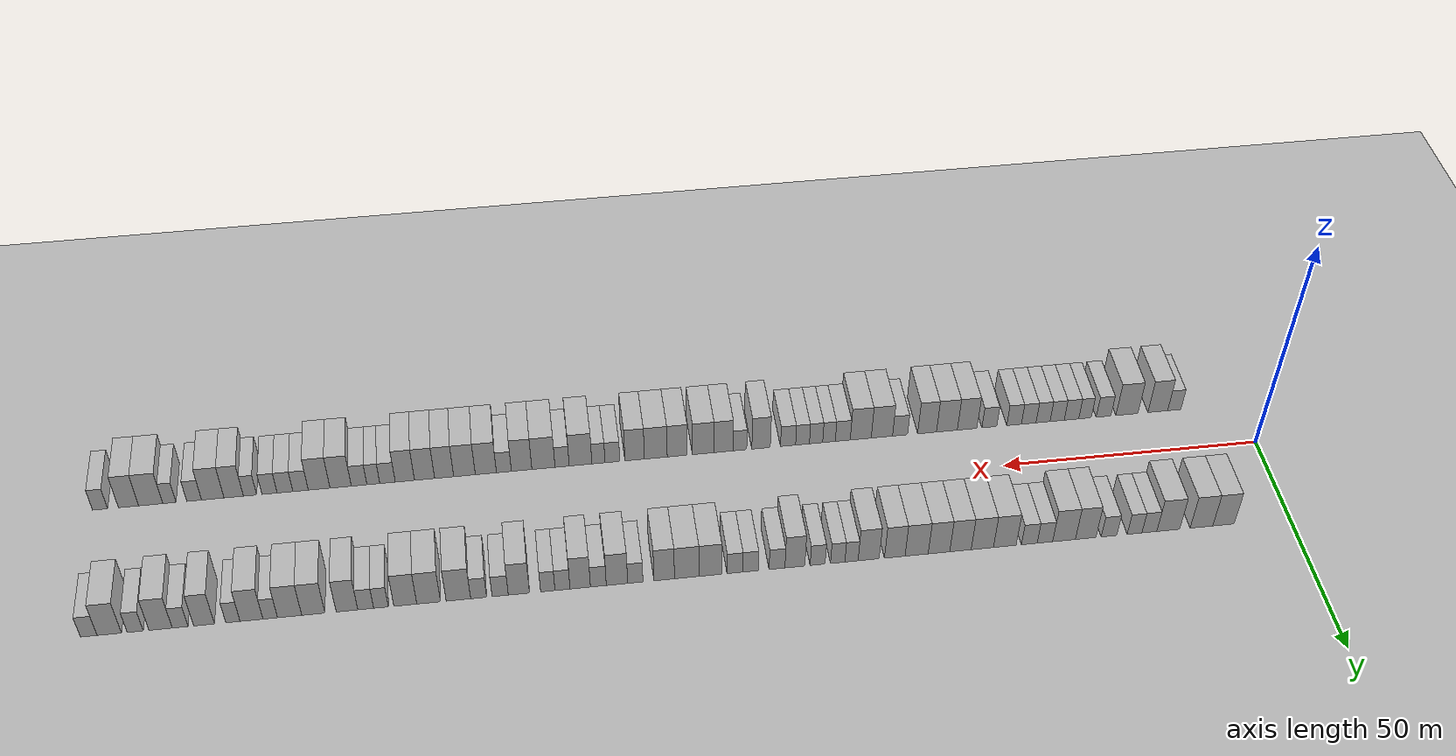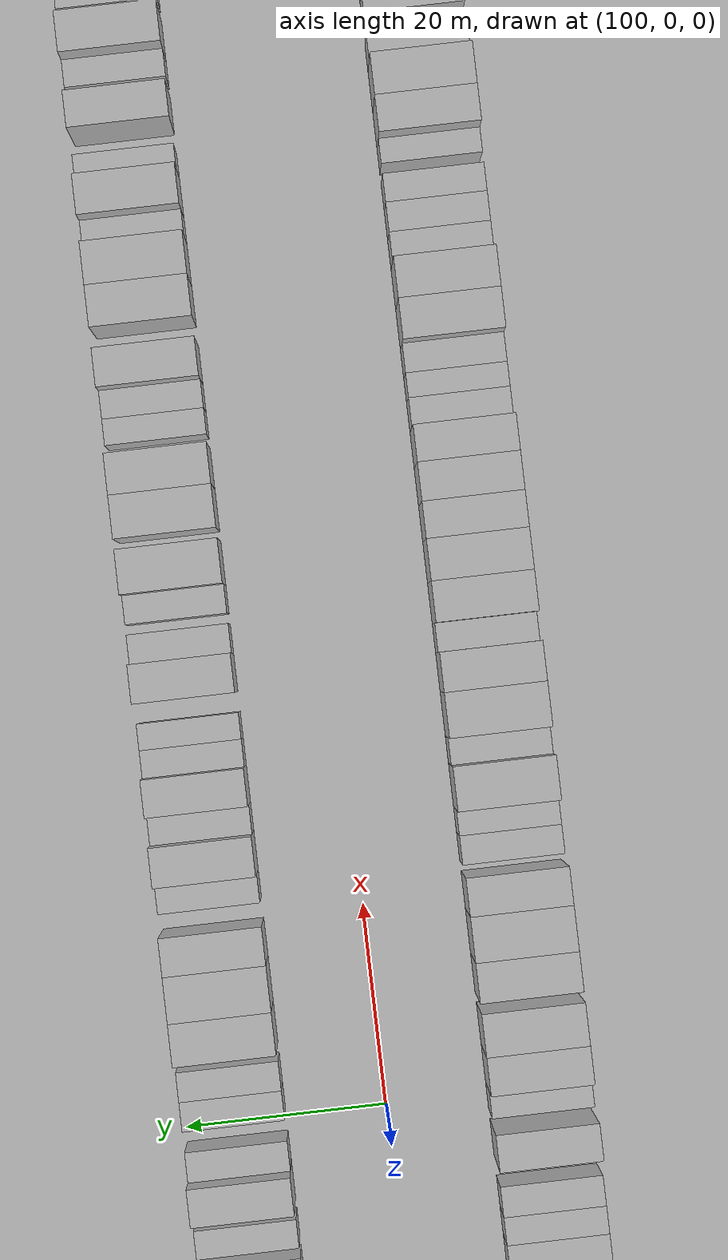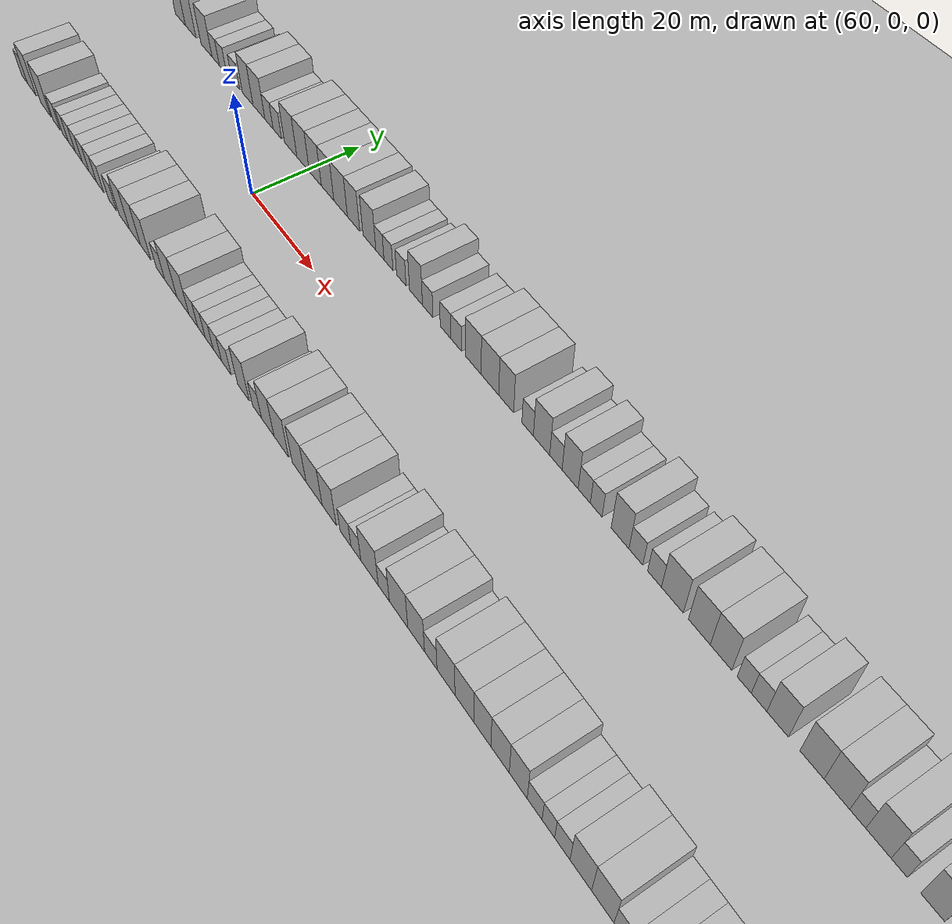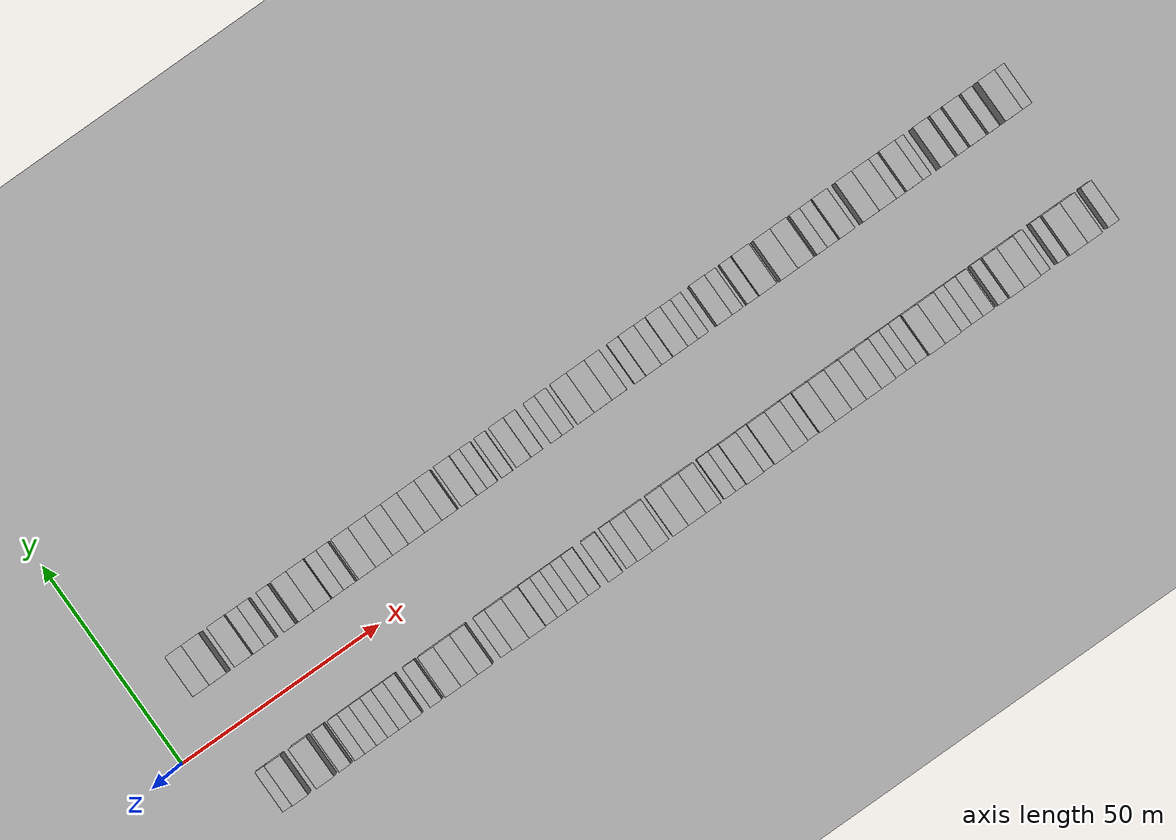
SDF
<?xml version="1.0" encoding="utf-8"?>

<sdf version="1.6">

   <world name="default">

      <gui fullscreen="0">

         <camera name="user_camera">

            <pose>-15 0 4.57585 0 0 0</pose>

            <view_controller>orbit</view_controller>

         </camera>

      </gui>

      <scene>

         <sky>

           <clouds>

             <speed>12</speed>

           </clouds>

         </sky>

         <ambient>0.4 0.4 0.4 1</ambient>

         <background>0.7 0.7 0.7 1</background>

         <shadows>1</shadows>

      </scene>

      <gravity>0 0 -9.8066</gravity>

      <magnetic_field>6e-06 2.3e-05 -4.2e-05</magnetic_field>

      <physics default="0" name="default_physics" type="ode">

         <ode>

            <solver>

               <type>quick</type>

               <iters>10</iters>

               <sor>1.0</sor>

               <use_dynamic_moi_rescaling>0</use_dynamic_moi_rescaling>

            </solver>

            <constraints>

               <cfm>0</cfm>

               <erp>0.2</erp>

               <contact_max_correcting_vel>100</contact_max_correcting_vel>

               <contact_surface_layer>0.001</contact_surface_layer>

            </constraints>

         </ode>

         <max_step_size>0.004</max_step_size>

         <real_time_factor>1</real_time_factor>

         <real_time_update_rate>250</real_time_update_rate>

      </physics>

      <light name="sun" type="directional">

         <cast_shadows>1</cast_shadows>

         <pose>0 0 10 0 0 0</pose>

         <diffuse>0.8 0.8 0.8 1</diffuse>

         <specular>0.2 0.2 0.2 1</specular>

         <attenuation>

            <range>1000</range>

            <constant>0.9</constant>

            <linear>0.01</linear>

            <quadratic>0.001</quadratic>

         </attenuation>

         <direction>-0.5 0.1 -0.9</direction>

      </light>

      <include>

         <name>ground_plane_1</name>

         <uri>model://HANNAS_ground_plane</uri>

         <pose>0 0 0  0 0 0</pose>

      </include>

      <include>

         <name>ground_plane_2</name>

         <uri>model://HANNAS_ground_plane</uri>

         <pose>100 0 0  0 0 0</pose>

      </include>

      <model name="building_1">

         <static>1</static>

         <pose frame="">13.0584 15.0000 0 0.000000 0.000000 1.570796</pose>

         <link name="link">

            <pose frame="">0 0 4.50 0 0 0</pose>

            <collision name="collision">

               <geometry>

                  <box>

                     <size>10.0000 4.1168 9.0000</size>

                  </box>

               </geometry>

               <max_contacts>10</max_contacts>

               <surface>

                  <contact>

                     <ode/>

                  </contact>

                  <bounce/>

                  <friction>

                     <torsional>

                        <ode/>

                     </torsional>

                     <ode/>

                  </friction>

               </surface>

            </collision>

            <visual name="visual">

               <cast_shadows>0</cast_shadows>

               <geometry>

                  <box>

                     <size>10.0000 4.1168 9.0000</size>

                  </box>

               </geometry>

               <material>

                  <script>

                     <uri>model://HANNAS_wall/materials/scripts</uri>

                     <uri>model://HANNAS_wall/materials/textures</uri>

                     <name>vrc/HANNAS_wall</name>

                  </script>

               </material>

            </visual>

            <self_collide>0</self_collide>

            <enable_wind>0</enable_wind>

            <kinematic>0</kinematic>

         </link>

      </model>

      <model name="building_2">

         <static>1</static>

         <pose frame="">17.2955 15.0000 0 0.000000 0.000000 1.570796</pose>

         <link name="link">

            <pose frame="">0 0 4.50 0 0 0</pose>

            <collision name="collision">

               <geometry>

                  <box>

                     <size>10.0000 4.3573 9.0000</size>

                  </box>

               </geometry>

               <max_contacts>10</max_contacts>

               <surface>

                  <contact>

                     <ode/>

                  </contact>

                  <bounce/>

                  <friction>

                     <torsional>

                        <ode/>

                     </torsional>

                     <ode/>

                  </friction>

               </surface>

            </collision>

            <visual name="visual">

               <cast_shadows>0</cast_shadows>

               <geometry>

                  <box>

                     <size>10.0000 4.3573 9.0000</size>

                  </box>

               </geometry>

               <material>

                  <script>

                     <uri>model://HANNAS_wall/materials/scripts</uri>

                     <uri>model://HANNAS_wall/materials/textures</uri>

                     <name>vrc/HANNAS_wall</name>

                  </script>

               </material>

            </visual>

            <self_collide>0</self_collide>

            <enable_wind>0</enable_wind>

            <kinematic>0</kinematic>

         </link>

      </model>

      <model name="building_3">

         <static>1</static>

         <pose frame="">23.6623 15.0000 0 0.000000 0.000000 1.570796</pose>

         <link name="link">

            <pose frame="">0 0 4.50 0 0 0</pose>

            <collision name="collision">

               <geometry>

                  <box>

                     <size>10.0000 4.3765 9.0000</size>

                  </box>

               </geometry>

               <max_contacts>10</max_contacts>

               <surface>

                  <contact>

                     <ode/>

                  </contact>

                  <bounce/>

                  <friction>

                     <torsional>

                        <ode/>

                     </torsional>

                     <ode/>

                  </friction>

               </surface>

            </collision>

            <visual name="visual">

               <cast_shadows>0</cast_shadows>

               <geometry>

                  <box>

                     <size>10.0000 4.3765 9.0000</size>

                  </box>

               </geometry>

               <material>

                  <script>

                     <uri>model://HANNAS_wall/materials/scripts</uri>

                     <uri>model://HANNAS_wall/materials/textures</uri>

                     <name>vrc/HANNAS_wall</name>

                  </script>

               </material>

            </visual>

            <self_collide>0</self_collide>

            <enable_wind>0</enable_wind>

            <kinematic>0</kinematic>

         </link>

      </model>

      <model name="building_4">

         <static>1</static>

         <pose frame="">27.2714 15.0000 0 0.000000 0.000000 1.570796</pose>

         <link name="link">

            <pose frame="">0 0 3.00 0 0 0</pose>

            <collision name="collision">

               <geometry>

                  <box>

                     <size>10.0000 2.8415 6.0000</size>

                  </box>

               </geometry>

               <max_contacts>10</max_contacts>

               <surface>

                  <contact>

                     <ode/>

                  </contact>

                  <bounce/>

                  <friction>

                     <torsional>

                        <ode/>

                     </torsional>

                     <ode/>

                  </friction>

               </surface>

            </collision>

            <visual name="visual">

               <cast_shadows>0</cast_shadows>

               <geometry>

                  <box>

                     <size>10.0000 2.8415 6.0000</size>

                  </box>

               </geometry>

               <material>

                  <script>

                     <uri>model://HANNAS_wall/materials/scripts</uri>

                     <uri>model://HANNAS_wall/materials/textures</uri>

                     <name>vrc/HANNAS_wall</name>

                  </script>

               </material>

            </visual>

            <self_collide>0</self_collide>

            <enable_wind>0</enable_wind>

            <kinematic>0</kinematic>

         </link>

      </model>

      <model name="building_5">

         <static>1</static>

         <pose frame="">30.1008 15.0000 0 0.000000 0.000000 1.570796</pose>

         <link name="link">

            <pose frame="">0 0 3.00 0 0 0</pose>

            <collision name="collision">

               <geometry>

                  <box>

                     <size>10.0000 2.8173 6.0000</size>

                  </box>

               </geometry>

               <max_contacts>10</max_contacts>

               <surface>

                  <contact>

                     <ode/>

                  </contact>

                  <bounce/>

                  <friction>

                     <torsional>

                        <ode/>

                     </torsional>

                     <ode/>

                  </friction>

               </surface>

            </collision>

            <visual name="visual">

               <cast_shadows>0</cast_shadows>

               <geometry>

                  <box>

                     <size>10.0000 2.8173 6.0000</size>

                  </box>

               </geometry>

               <material>

                  <script>

                     <uri>model://HANNAS_wall/materials/scripts</uri>

                     <uri>model://HANNAS_wall/materials/textures</uri>

                     <name>vrc/HANNAS_wall</name>

                  </script>

               </material>

            </visual>

            <self_collide>0</self_collide>

            <enable_wind>0</enable_wind>

            <kinematic>0</kinematic>

         </link>

      </model>

      <model name="building_6">

         <static>1</static>

         <pose frame="">34.9873 15.0000 0 0.000000 0.000000 1.570796</pose>

         <link name="link">

            <pose frame="">0 0 3.00 0 0 0</pose>

            <collision name="collision">

               <geometry>

                  <box>

                     <size>10.0000 2.9558 6.0000</size>

                  </box>

               </geometry>

               <max_contacts>10</max_contacts>

               <surface>

                  <contact>

                     <ode/>

                  </contact>

                  <bounce/>

                  <friction>

                     <torsional>

                        <ode/>

                     </torsional>

                     <ode/>

                  </friction>

               </surface>

            </collision>

            <visual name="visual">

               <cast_shadows>0</cast_shadows>

               <geometry>

                  <box>

                     <size>10.0000 2.9558 6.0000</size>

                  </box>

               </geometry>

               <material>

                  <script>

                     <uri>model://HANNAS_wall/materials/scripts</uri>

                     <uri>model://HANNAS_wall/materials/textures</uri>

                     <name>vrc/HANNAS_wall</name>

                  </script>

               </material>

            </visual>

            <self_collide>0</self_collide>

            <enable_wind>0</enable_wind>

            <kinematic>0</kinematic>

         </link>

      </model>

      <model name="building_7">

         <static>1</static>

         <pose frame="">39.4198 15.0000 0 0.000000 0.000000 1.570796</pose>

         <link name="link">

            <pose frame="">0 0 4.50 0 0 0</pose>

            <collision name="collision">

               <geometry>

                  <box>

                     <size>10.0000 3.9092 9.0000</size>

                  </box>

               </geometry>

               <max_contacts>10</max_contacts>

               <surface>

                  <contact>

                     <ode/>

                  </contact>

                  <bounce/>

                  <friction>

                     <torsional>

                        <ode/>

                     </torsional>

                     <ode/>

                  </friction>

               </surface>

            </collision>

            <visual name="visual">

               <cast_shadows>0</cast_shadows>

               <geometry>

                  <box>

                     <size>10.0000 3.9092 9.0000</size>

                  </box>

               </geometry>

               <material>

                  <script>

                     <uri>model://HANNAS_wall/materials/scripts</uri>

                     <uri>model://HANNAS_wall/materials/textures</uri>

                     <name>vrc/HANNAS_wall</name>

                  </script>

               </material>

            </visual>

            <self_collide>0</self_collide>

            <enable_wind>0</enable_wind>

            <kinematic>0</kinematic>

         </link>

      </model>

      <model name="building_8">

         <static>1</static>

         <pose frame="">43.5342 15.0000 0 0.000000 0.000000 1.570796</pose>

         <link name="link">

            <pose frame="">0 0 4.50 0 0 0</pose>

            <collision name="collision">

               <geometry>

                  <box>

                     <size>10.0000 4.3196 9.0000</size>

                  </box>

               </geometry>

               <max_contacts>10</max_contacts>

               <surface>

                  <contact>

                     <ode/>

                  </contact>

                  <bounce/>

                  <friction>

                     <torsional>

                        <ode/>

                     </torsional>

                     <ode/>

                  </friction>

               </surface>

            </collision>

            <visual name="visual">

               <cast_shadows>0</cast_shadows>

               <geometry>

                  <box>

                     <size>10.0000 4.3196 9.0000</size>

                  </box>

               </geometry>

               <material>

                  <script>

                     <uri>model://HANNAS_wall/materials/scripts</uri>

                     <uri>model://HANNAS_wall/materials/textures</uri>

                     <name>vrc/HANNAS_wall</name>

                  </script>

               </material>

            </visual>

            <self_collide>0</self_collide>

            <enable_wind>0</enable_wind>

            <kinematic>0</kinematic>

         </link>

      </model>

      <model name="building_9">

         <static>1</static>

         <pose frame="">47.1552 15.0000 0 0.000000 0.000000 1.570796</pose>

         <link name="link">

            <pose frame="">0 0 3.00 0 0 0</pose>

            <collision name="collision">

               <geometry>

                  <box>

                     <size>10.0000 2.9224 6.0000</size>

                  </box>

               </geometry>

               <max_contacts>10</max_contacts>

               <surface>

                  <contact>

                     <ode/>

                  </contact>

                  <bounce/>

                  <friction>

                     <torsional>

                        <ode/>

                     </torsional>

                     <ode/>

                  </friction>

               </surface>

            </collision>

            <visual name="visual">

               <cast_shadows>0</cast_shadows>

               <geometry>

                  <box>

                     <size>10.0000 2.9224 6.0000</size>

                  </box>

               </geometry>

               <material>

                  <script>

                     <uri>model://HANNAS_wall/materials/scripts</uri>

                     <uri>model://HANNAS_wall/materials/textures</uri>

                     <name>vrc/HANNAS_wall</name>

                  </script>

               </material>

            </visual>

            <self_collide>0</self_collide>

            <enable_wind>0</enable_wind>

            <kinematic>0</kinematic>

         </link>

      </model>

      <model name="building_10">

         <static>1</static>

         <pose frame="">50.1067 15.0000 0 0.000000 0.000000 1.570796</pose>

         <link name="link">

            <pose frame="">0 0 3.00 0 0 0</pose>

            <collision name="collision">

               <geometry>

                  <box>

                     <size>10.0000 2.9807 6.0000</size>

                  </box>

               </geometry>

               <max_contacts>10</max_contacts>

               <surface>

                  <contact>

                     <ode/>

                  </contact>

                  <bounce/>

                  <friction>

                     <torsional>

                        <ode/>

                     </torsional>

                     <ode/>

                  </friction>

               </surface>

            </collision>

            <visual name="visual">

               <cast_shadows>0</cast_shadows>

               <geometry>

                  <box>

                     <size>10.0000 2.9807 6.0000</size>

                  </box>

               </geometry>

               <material>

                  <script>

                     <uri>model://HANNAS_wall/materials/scripts</uri>

                     <uri>model://HANNAS_wall/materials/textures</uri>

                     <name>vrc/HANNAS_wall</name>

                  </script>

               </material>

            </visual>

            <self_collide>0</self_collide>

            <enable_wind>0</enable_wind>

            <kinematic>0</kinematic>

         </link>

      </model>

      <model name="building_11">

         <static>1</static>

         <pose frame="">54.7344 15.0000 0 0.000000 0.000000 1.570796</pose>

         <link name="link">

            <pose frame="">0 0 4.50 0 0 0</pose>

            <collision name="collision">

               <geometry>

                  <box>

                     <size>10.0000 4.2747 9.0000</size>

                  </box>

               </geometry>

               <max_contacts>10</max_contacts>

               <surface>

                  <contact>

                     <ode/>

                  </contact>

                  <bounce/>

                  <friction>

                     <torsional>

                        <ode/>

                     </torsional>

                     <ode/>

                  </friction>

               </surface>

            </collision>

            <visual name="visual">

               <cast_shadows>0</cast_shadows>

               <geometry>

                  <box>

                     <size>10.0000 4.2747 9.0000</size>

                  </box>

               </geometry>

               <material>

                  <script>

                     <uri>model://HANNAS_wall/materials/scripts</uri>

                     <uri>model://HANNAS_wall/materials/textures</uri>

                     <name>vrc/HANNAS_wall</name>

                  </script>

               </material>

            </visual>

            <self_collide>0</self_collide>

            <enable_wind>0</enable_wind>

            <kinematic>0</kinematic>

         </link>

      </model>

      <model name="building_12">

         <static>1</static>

         <pose frame="">58.9776 15.0000 0 0.000000 0.000000 1.570796</pose>

         <link name="link">

            <pose frame="">0 0 4.50 0 0 0</pose>

            <collision name="collision">

               <geometry>

                  <box>

                     <size>10.0000 4.2117 9.0000</size>

                  </box>

               </geometry>

               <max_contacts>10</max_contacts>

               <surface>

                  <contact>

                     <ode/>

                  </contact>

                  <bounce/>

                  <friction>

                     <torsional>

                        <ode/>

                     </torsional>

                     <ode/>

                  </friction>

               </surface>

            </collision>

            <visual name="visual">

               <cast_shadows>0</cast_shadows>

               <geometry>

                  <box>

                     <size>10.0000 4.2117 9.0000</size>

                  </box>

               </geometry>

               <material>

                  <script>

                     <uri>model://HANNAS_wall/materials/scripts</uri>

                     <uri>model://HANNAS_wall/materials/textures</uri>

                     <name>vrc/HANNAS_wall</name>

                  </script>

               </material>

            </visual>

            <self_collide>0</self_collide>

            <enable_wind>0</enable_wind>

            <kinematic>0</kinematic>

         </link>

      </model>

      <model name="building_13">

         <static>1</static>

         <pose frame="">63.0904 15.0000 0 0.000000 0.000000 1.570796</pose>

         <link name="link">

            <pose frame="">0 0 4.50 0 0 0</pose>

            <collision name="collision">

               <geometry>

                  <box>

                     <size>10.0000 4.0140 9.0000</size>

                  </box>

               </geometry>

               <max_contacts>10</max_contacts>

               <surface>

                  <contact>

                     <ode/>

                  </contact>

                  <bounce/>

                  <friction>

                     <torsional>

                        <ode/>

                     </torsional>

                     <ode/>

                  </friction>

               </surface>

            </collision>

            <visual name="visual">

               <cast_shadows>0</cast_shadows>

               <geometry>

                  <box>

                     <size>10.0000 4.0140 9.0000</size>

                  </box>

               </geometry>

               <material>

                  <script>

                     <uri>model://HANNAS_wall/materials/scripts</uri>

                     <uri>model://HANNAS_wall/materials/textures</uri>

                     <name>vrc/HANNAS_wall</name>

                  </script>

               </material>

            </visual>

            <self_collide>0</self_collide>

            <enable_wind>0</enable_wind>

            <kinematic>0</kinematic>

         </link>

      </model>

      <model name="building_14">

         <static>1</static>

         <pose frame="">67.1182 15.0000 0 0.000000 0.000000 1.570796</pose>

         <link name="link">

            <pose frame="">0 0 4.50 0 0 0</pose>

            <collision name="collision">

               <geometry>

                  <box>

                     <size>10.0000 4.0417 9.0000</size>

                  </box>

               </geometry>

               <max_contacts>10</max_contacts>

               <surface>

                  <contact>

                     <ode/>

                  </contact>

                  <bounce/>

                  <friction>

                     <torsional>

                        <ode/>

                     </torsional>

                     <ode/>

                  </friction>

               </surface>

            </collision>

            <visual name="visual">

               <cast_shadows>0</cast_shadows>

               <geometry>

                  <box>

                     <size>10.0000 4.0417 9.0000</size>

                  </box>

               </geometry>

               <material>

                  <script>

                     <uri>model://HANNAS_wall/materials/scripts</uri>

                     <uri>model://HANNAS_wall/materials/textures</uri>

                     <name>vrc/HANNAS_wall</name>

                  </script>

               </material>

            </visual>

            <self_collide>0</self_collide>

            <enable_wind>0</enable_wind>

            <kinematic>0</kinematic>

         </link>

      </model>

      <model name="building_15">

         <static>1</static>

         <pose frame="">71.3008 15.0000 0 0.000000 0.000000 1.570796</pose>

         <link name="link">

            <pose frame="">0 0 4.50 0 0 0</pose>

            <collision name="collision">

               <geometry>

                  <box>

                     <size>10.0000 4.3233 9.0000</size>

                  </box>

               </geometry>

               <max_contacts>10</max_contacts>

               <surface>

                  <contact>

                     <ode/>

                  </contact>

                  <bounce/>

                  <friction>

                     <torsional>

                        <ode/>

                     </torsional>

                     <ode/>

                  </friction>

               </surface>

            </collision>

            <visual name="visual">

               <cast_shadows>0</cast_shadows>

               <geometry>

                  <box>

                     <size>10.0000 4.3233 9.0000</size>

                  </box>

               </geometry>

               <material>

                  <script>

                     <uri>model://HANNAS_wall/materials/scripts</uri>

                     <uri>model://HANNAS_wall/materials/textures</uri>

                     <name>vrc/HANNAS_wall</name>

                  </script>

               </material>

            </visual>

            <self_collide>0</self_collide>

            <enable_wind>0</enable_wind>

            <kinematic>0</kinematic>

         </link>

      </model>

      <model name="building_16">

         <static>1</static>

         <pose frame="">75.3823 15.0000 0 0.000000 0.000000 1.570796</pose>

         <link name="link">

            <pose frame="">0 0 4.50 0 0 0</pose>

            <collision name="collision">

               <geometry>

                  <box>

                     <size>10.0000 3.8398 9.0000</size>

                  </box>

               </geometry>

               <max_contacts>10</max_contacts>

               <surface>

                  <contact>

                     <ode/>

                  </contact>

                  <bounce/>

                  <friction>

                     <torsional>

                        <ode/>

                     </torsional>

                     <ode/>

                  </friction>

               </surface>

            </collision>

            <visual name="visual">

               <cast_shadows>0</cast_shadows>

               <geometry>

                  <box>

                     <size>10.0000 3.8398 9.0000</size>

                  </box>

               </geometry>

               <material>

                  <script>

                     <uri>model://HANNAS_wall/materials/scripts</uri>

                     <uri>model://HANNAS_wall/materials/textures</uri>

                     <name>vrc/HANNAS_wall</name>

                  </script>

               </material>

            </visual>

            <self_collide>0</self_collide>

            <enable_wind>0</enable_wind>

            <kinematic>0</kinematic>

         </link>

      </model>

      <model name="building_17">

         <static>1</static>

         <pose frame="">80.2570 15.0000 0 0.000000 0.000000 1.570796</pose>

         <link name="link">

            <pose frame="">0 0 4.50 0 0 0</pose>

            <collision name="collision">

               <geometry>

                  <box>

                     <size>10.0000 3.9096 9.0000</size>

                  </box>

               </geometry>

               <max_contacts>10</max_contacts>

               <surface>

                  <contact>

                     <ode/>

                  </contact>

                  <bounce/>

                  <friction>

                     <torsional>

                        <ode/>

                     </torsional>

                     <ode/>

                  </friction>

               </surface>

            </collision>

            <visual name="visual">

               <cast_shadows>0</cast_shadows>

               <geometry>

                  <box>

                     <size>10.0000 3.9096 9.0000</size>

                  </box>

               </geometry>

               <material>

                  <script>

                     <uri>model://HANNAS_wall/materials/scripts</uri>

                     <uri>model://HANNAS_wall/materials/textures</uri>

                     <name>vrc/HANNAS_wall</name>

                  </script>

               </material>

            </visual>

            <self_collide>0</self_collide>

            <enable_wind>0</enable_wind>

            <kinematic>0</kinematic>

         </link>

      </model>

      <model name="building_18">

         <static>1</static>

         <pose frame="">83.4359 15.0000 0 0.000000 0.000000 1.570796</pose>

         <link name="link">

            <pose frame="">0 0 3.00 0 0 0</pose>

            <collision name="collision">

               <geometry>

                  <box>

                     <size>10.0000 2.4482 6.0000</size>

                  </box>

               </geometry>

               <max_contacts>10</max_contacts>

               <surface>

                  <contact>

                     <ode/>

                  </contact>

                  <bounce/>

                  <friction>

                     <torsional>

                        <ode/>

                     </torsional>

                     <ode/>

                  </friction>

               </surface>

            </collision>

            <visual name="visual">

               <cast_shadows>0</cast_shadows>

               <geometry>

                  <box>

                     <size>10.0000 2.4482 6.0000</size>

                  </box>

               </geometry>

               <material>

                  <script>

                     <uri>model://HANNAS_wall/materials/scripts</uri>

                     <uri>model://HANNAS_wall/materials/textures</uri>

                     <name>vrc/HANNAS_wall</name>

                  </script>

               </material>

            </visual>

            <self_collide>0</self_collide>

            <enable_wind>0</enable_wind>

            <kinematic>0</kinematic>

         </link>

      </model>

      <model name="building_19">

         <static>1</static>

         <pose frame="">86.0006 15.0000 0 0.000000 0.000000 1.570796</pose>

         <link name="link">

            <pose frame="">0 0 3.00 0 0 0</pose>

            <collision name="collision">

               <geometry>

                  <box>

                     <size>10.0000 2.6813 6.0000</size>

                  </box>

               </geometry>

               <max_contacts>10</max_contacts>

               <surface>

                  <contact>

                     <ode/>

                  </contact>

                  <bounce/>

                  <friction>

                     <torsional>

                        <ode/>

                     </torsional>

                     <ode/>

                  </friction>

               </surface>

            </collision>

            <visual name="visual">

               <cast_shadows>0</cast_shadows>

               <geometry>

                  <box>

                     <size>10.0000 2.6813 6.0000</size>

                  </box>

               </geometry>

               <material>

                  <script>

                     <uri>model://HANNAS_wall/materials/scripts</uri>

                     <uri>model://HANNAS_wall/materials/textures</uri>

                     <name>vrc/HANNAS_wall</name>

                  </script>

               </material>

            </visual>

            <self_collide>0</self_collide>

            <enable_wind>0</enable_wind>

            <kinematic>0</kinematic>

         </link>

      </model>

      <model name="building_20">

         <static>1</static>

         <pose frame="">89.7267 15.0000 0 0.000000 0.000000 1.570796</pose>

         <link name="link">

            <pose frame="">0 0 3.00 0 0 0</pose>

            <collision name="collision">

               <geometry>

                  <box>

                     <size>10.0000 2.7710 6.0000</size>

                  </box>

               </geometry>

               <max_contacts>10</max_contacts>

               <surface>

                  <contact>

                     <ode/>

                  </contact>

                  <bounce/>

                  <friction>

                     <torsional>

                        <ode/>

                     </torsional>

                     <ode/>

                  </friction>

               </surface>

            </collision>

            <visual name="visual">

               <cast_shadows>0</cast_shadows>

               <geometry>

                  <box>

                     <size>10.0000 2.7710 6.0000</size>

                  </box>

               </geometry>

               <material>

                  <script>

                     <uri>model://HANNAS_wall/materials/scripts</uri>

                     <uri>model://HANNAS_wall/materials/textures</uri>

                     <name>vrc/HANNAS_wall</name>

                  </script>

               </material>

            </visual>

            <self_collide>0</self_collide>

            <enable_wind>0</enable_wind>

            <kinematic>0</kinematic>

         </link>

      </model>

      <model name="building_21">

         <static>1</static>

         <pose frame="">93.9495 15.0000 0 0.000000 0.000000 1.570796</pose>

         <link name="link">

            <pose frame="">0 0 4.50 0 0 0</pose>

            <collision name="collision">

               <geometry>

                  <box>

                     <size>10.0000 3.6744 9.0000</size>

                  </box>

               </geometry>

               <max_contacts>10</max_contacts>

               <surface>

                  <contact>

                     <ode/>

                  </contact>

                  <bounce/>

                  <friction>

                     <torsional>

                        <ode/>

                     </torsional>

                     <ode/>

                  </friction>

               </surface>

            </collision>

            <visual name="visual">

               <cast_shadows>0</cast_shadows>

               <geometry>

                  <box>

                     <size>10.0000 3.6744 9.0000</size>

                  </box>

               </geometry>

               <material>

                  <script>

                     <uri>model://HANNAS_wall/materials/scripts</uri>

                     <uri>model://HANNAS_wall/materials/textures</uri>

                     <name>vrc/HANNAS_wall</name>

                  </script>

               </material>

            </visual>

            <self_collide>0</self_collide>

            <enable_wind>0</enable_wind>

            <kinematic>0</kinematic>

         </link>

      </model>

      <model name="building_22">

         <static>1</static>

         <pose frame="">97.2493 15.0000 0 0.000000 0.000000 1.570796</pose>

         <link name="link">

            <pose frame="">0 0 3.00 0 0 0</pose>

            <collision name="collision">

               <geometry>

                  <box>

                     <size>10.0000 2.9253 6.0000</size>

                  </box>

               </geometry>

               <max_contacts>10</max_contacts>

               <surface>

                  <contact>

                     <ode/>

                  </contact>

                  <bounce/>

                  <friction>

                     <torsional>

                        <ode/>

                     </torsional>

                     <ode/>

                  </friction>

               </surface>

            </collision>

            <visual name="visual">

               <cast_shadows>0</cast_shadows>

               <geometry>

                  <box>

                     <size>10.0000 2.9253 6.0000</size>

                  </box>

               </geometry>

               <material>

                  <script>

                     <uri>model://HANNAS_wall/materials/scripts</uri>

                     <uri>model://HANNAS_wall/materials/textures</uri>

                     <name>vrc/HANNAS_wall</name>

                  </script>

               </material>

            </visual>

            <self_collide>0</self_collide>

            <enable_wind>0</enable_wind>

            <kinematic>0</kinematic>

         </link>

      </model>

      <model name="building_23">

         <static>1</static>

         <pose frame="">102.1418 15.0000 0 0.000000 0.000000 1.570796</pose>

         <link name="link">

            <pose frame="">0 0 3.00 0 0 0</pose>

            <collision name="collision">

               <geometry>

                  <box>

                     <size>10.0000 2.8597 6.0000</size>

                  </box>

               </geometry>

               <max_contacts>10</max_contacts>

               <surface>

                  <contact>

                     <ode/>

                  </contact>

                  <bounce/>

                  <friction>

                     <torsional>

                        <ode/>

                     </torsional>

                     <ode/>

                  </friction>

               </surface>

            </collision>

            <visual name="visual">

               <cast_shadows>0</cast_shadows>

               <geometry>

                  <box>

                     <size>10.0000 2.8597 6.0000</size>

                  </box>

               </geometry>

               <material>

                  <script>

                     <uri>model://HANNAS_wall/materials/scripts</uri>

                     <uri>model://HANNAS_wall/materials/textures</uri>

                     <name>vrc/HANNAS_wall</name>

                  </script>

               </material>

            </visual>

            <self_collide>0</self_collide>

            <enable_wind>0</enable_wind>

            <kinematic>0</kinematic>

         </link>

      </model>

      <model name="building_24">

         <static>1</static>

         <pose frame="">105.0148 15.0000 0 0.000000 0.000000 1.570796</pose>

         <link name="link">

            <pose frame="">0 0 3.00 0 0 0</pose>

            <collision name="collision">

               <geometry>

                  <box>

                     <size>10.0000 2.8864 6.0000</size>

                  </box>

               </geometry>

               <max_contacts>10</max_contacts>

               <surface>

                  <contact>

                     <ode/>

                  </contact>

                  <bounce/>

                  <friction>

                     <torsional>

                        <ode/>

                     </torsional>

                     <ode/>

                  </friction>

               </surface>

            </collision>

            <visual name="visual">

               <cast_shadows>0</cast_shadows>

               <geometry>

                  <box>

                     <size>10.0000 2.8864 6.0000</size>

                  </box>

               </geometry>

               <material>

                  <script>

                     <uri>model://HANNAS_wall/materials/scripts</uri>

                     <uri>model://HANNAS_wall/materials/textures</uri>

                     <name>vrc/HANNAS_wall</name>

                  </script>

               </material>

            </visual>

            <self_collide>0</self_collide>

            <enable_wind>0</enable_wind>

            <kinematic>0</kinematic>

         </link>

      </model>

      <model name="building_25">

         <static>1</static>

         <pose frame="">109.5327 15.0000 0 0.000000 0.000000 1.570796</pose>

         <link name="link">

            <pose frame="">0 0 4.50 0 0 0</pose>

            <collision name="collision">

               <geometry>

                  <box>

                     <size>10.0000 4.1493 9.0000</size>

                  </box>

               </geometry>

               <max_contacts>10</max_contacts>

               <surface>

                  <contact>

                     <ode/>

                  </contact>

                  <bounce/>

                  <friction>

                     <torsional>

                        <ode/>

                     </torsional>

                     <ode/>

                  </friction>

               </surface>

            </collision>

            <visual name="visual">

               <cast_shadows>0</cast_shadows>

               <geometry>

                  <box>

                     <size>10.0000 4.1493 9.0000</size>

                  </box>

               </geometry>

               <material>

                  <script>

                     <uri>model://HANNAS_wall/materials/scripts</uri>

                     <uri>model://HANNAS_wall/materials/textures</uri>

                     <name>vrc/HANNAS_wall</name>

                  </script>

               </material>

            </visual>

            <self_collide>0</self_collide>

            <enable_wind>0</enable_wind>

            <kinematic>0</kinematic>

         </link>

      </model>

      <model name="building_26">

         <static>1</static>

         <pose frame="">113.8534 15.0000 0 0.000000 0.000000 1.570796</pose>

         <link name="link">

            <pose frame="">0 0 4.50 0 0 0</pose>

            <collision name="collision">

               <geometry>

                  <box>

                     <size>10.0000 4.4923 9.0000</size>

                  </box>

               </geometry>

               <max_contacts>10</max_contacts>

               <surface>

                  <contact>

                     <ode/>

                  </contact>

                  <bounce/>

                  <friction>

                     <torsional>

                        <ode/>

                     </torsional>

                     <ode/>

                  </friction>

               </surface>

            </collision>

            <visual name="visual">

               <cast_shadows>0</cast_shadows>

               <geometry>

                  <box>

                     <size>10.0000 4.4923 9.0000</size>

                  </box>

               </geometry>

               <material>

                  <script>

                     <uri>model://HANNAS_wall/materials/scripts</uri>

                     <uri>model://HANNAS_wall/materials/textures</uri>

                     <name>vrc/HANNAS_wall</name>

                  </script>

               </material>

            </visual>

            <self_collide>0</self_collide>

            <enable_wind>0</enable_wind>

            <kinematic>0</kinematic>

         </link>

      </model>

      <model name="building_27">

         <static>1</static>

         <pose frame="">117.9723 15.0000 0 0.000000 0.000000 1.570796</pose>

         <link name="link">

            <pose frame="">0 0 4.50 0 0 0</pose>

            <collision name="collision">

               <geometry>

                  <box>

                     <size>10.0000 3.7454 9.0000</size>

                  </box>

               </geometry>

               <max_contacts>10</max_contacts>

               <surface>

                  <contact>

                     <ode/>

                  </contact>

                  <bounce/>

                  <friction>

                     <torsional>

                        <ode/>

                     </torsional>

                     <ode/>

                  </friction>

               </surface>

            </collision>

            <visual name="visual">

               <cast_shadows>0</cast_shadows>

               <geometry>

                  <box>

                     <size>10.0000 3.7454 9.0000</size>

                  </box>

               </geometry>

               <material>

                  <script>

                     <uri>model://HANNAS_wall/materials/scripts</uri>

                     <uri>model://HANNAS_wall/materials/textures</uri>

                     <name>vrc/HANNAS_wall</name>

                  </script>

               </material>

            </visual>

            <self_collide>0</self_collide>

            <enable_wind>0</enable_wind>

            <kinematic>0</kinematic>

         </link>

      </model>

      <model name="building_28">

         <static>1</static>

         <pose frame="">123.2405 15.0000 0 0.000000 0.000000 1.570796</pose>

         <link name="link">

            <pose frame="">0 0 3.00 0 0 0</pose>

            <collision name="collision">

               <geometry>

                  <box>

                     <size>10.0000 2.7911 6.0000</size>

                  </box>

               </geometry>

               <max_contacts>10</max_contacts>

               <surface>

                  <contact>

                     <ode/>

                  </contact>

                  <bounce/>

                  <friction>

                     <torsional>

                        <ode/>

                     </torsional>

                     <ode/>

                  </friction>

               </surface>

            </collision>

            <visual name="visual">

               <cast_shadows>0</cast_shadows>

               <geometry>

                  <box>

                     <size>10.0000 2.7911 6.0000</size>

                  </box>

               </geometry>

               <material>

                  <script>

                     <uri>model://HANNAS_wall/materials/scripts</uri>

                     <uri>model://HANNAS_wall/materials/textures</uri>

                     <name>vrc/HANNAS_wall</name>

                  </script>

               </material>

            </visual>

            <self_collide>0</self_collide>

            <enable_wind>0</enable_wind>

            <kinematic>0</kinematic>

         </link>

      </model>

      <model name="building_29">

         <static>1</static>

         <pose frame="">126.5817 15.0000 0 0.000000 0.000000 1.570796</pose>

         <link name="link">

            <pose frame="">0 0 4.50 0 0 0</pose>

            <collision name="collision">

               <geometry>

                  <box>

                     <size>10.0000 3.8913 9.0000</size>

                  </box>

               </geometry>

               <max_contacts>10</max_contacts>

               <surface>

                  <contact>

                     <ode/>

                  </contact>

                  <bounce/>

                  <friction>

                     <torsional>

                        <ode/>

                     </torsional>

                     <ode/>

                  </friction>

               </surface>

            </collision>

            <visual name="visual">

               <cast_shadows>0</cast_shadows>

               <geometry>

                  <box>

                     <size>10.0000 3.8913 9.0000</size>

                  </box>

               </geometry>

               <material>

                  <script>

                     <uri>model://HANNAS_wall/materials/scripts</uri>

                     <uri>model://HANNAS_wall/materials/textures</uri>

                     <name>vrc/HANNAS_wall</name>

                  </script>

               </material>

            </visual>

            <self_collide>0</self_collide>

            <enable_wind>0</enable_wind>

            <kinematic>0</kinematic>

         </link>

      </model>

      <model name="building_30">

         <static>1</static>

         <pose frame="">129.9661 15.0000 0 0.000000 0.000000 1.570796</pose>

         <link name="link">

            <pose frame="">0 0 3.00 0 0 0</pose>

            <collision name="collision">

               <geometry>

                  <box>

                     <size>10.0000 2.8775 6.0000</size>

                  </box>

               </geometry>

               <max_contacts>10</max_contacts>

               <surface>

                  <contact>

                     <ode/>

                  </contact>

                  <bounce/>

                  <friction>

                     <torsional>

                        <ode/>

                     </torsional>

                     <ode/>

                  </friction>

               </surface>

            </collision>

            <visual name="visual">

               <cast_shadows>0</cast_shadows>

               <geometry>

                  <box>

                     <size>10.0000 2.8775 6.0000</size>

                  </box>

               </geometry>

               <material>

                  <script>

                     <uri>model://HANNAS_wall/materials/scripts</uri>

                     <uri>model://HANNAS_wall/materials/textures</uri>

                     <name>vrc/HANNAS_wall</name>

                  </script>

               </material>

            </visual>

            <self_collide>0</self_collide>

            <enable_wind>0</enable_wind>

            <kinematic>0</kinematic>

         </link>

      </model>

      <model name="building_31">

         <static>1</static>

         <pose frame="">133.2513 15.0000 0 0.000000 0.000000 1.570796</pose>

         <link name="link">

            <pose frame="">0 0 4.50 0 0 0</pose>

            <collision name="collision">

               <geometry>

                  <box>

                     <size>10.0000 3.6928 9.0000</size>

                  </box>

               </geometry>

               <max_contacts>10</max_contacts>

               <surface>

                  <contact>

                     <ode/>

                  </contact>

                  <bounce/>

                  <friction>

                     <torsional>

                        <ode/>

                     </torsional>

                     <ode/>

                  </friction>

               </surface>

            </collision>

            <visual name="visual">

               <cast_shadows>0</cast_shadows>

               <geometry>

                  <box>

                     <size>10.0000 3.6928 9.0000</size>

                  </box>

               </geometry>

               <material>

                  <script>

                     <uri>model://HANNAS_wall/materials/scripts</uri>

                     <uri>model://HANNAS_wall/materials/textures</uri>

                     <name>vrc/HANNAS_wall</name>

                  </script>

               </material>

            </visual>

            <self_collide>0</self_collide>

            <enable_wind>0</enable_wind>

            <kinematic>0</kinematic>

         </link>

      </model>

      <model name="building_32">

         <static>1</static>

         <pose frame="">136.4618 15.0000 0 0.000000 0.000000 1.570796</pose>

         <link name="link">

            <pose frame="">0 0 3.00 0 0 0</pose>

            <collision name="collision">

               <geometry>

                  <box>

                     <size>10.0000 2.7283 6.0000</size>

                  </box>

               </geometry>

               <max_contacts>10</max_contacts>

               <surface>

                  <contact>

                     <ode/>

                  </contact>

                  <bounce/>

                  <friction>

                     <torsional>

                        <ode/>

                     </torsional>

                     <ode/>

                  </friction>

               </surface>

            </collision>

            <visual name="visual">

               <cast_shadows>0</cast_shadows>

               <geometry>

                  <box>

                     <size>10.0000 2.7283 6.0000</size>

                  </box>

               </geometry>

               <material>

                  <script>

                     <uri>model://HANNAS_wall/materials/scripts</uri>

                     <uri>model://HANNAS_wall/materials/textures</uri>

                     <name>vrc/HANNAS_wall</name>

                  </script>

               </material>

            </visual>

            <self_collide>0</self_collide>

            <enable_wind>0</enable_wind>

            <kinematic>0</kinematic>

         </link>

      </model>

      <model name="building_33">

         <static>1</static>

         <pose frame="">139.1239 15.0000 0 0.000000 0.000000 1.570796</pose>

         <link name="link">

            <pose frame="">0 0 3.00 0 0 0</pose>

            <collision name="collision">

               <geometry>

                  <box>

                     <size>10.0000 2.5960 6.0000</size>

                  </box>

               </geometry>

               <max_contacts>10</max_contacts>

               <surface>

                  <contact>

                     <ode/>

                  </contact>

                  <bounce/>

                  <friction>

                     <torsional>

                        <ode/>

                     </torsional>

                     <ode/>

                  </friction>

               </surface>

            </collision>

            <visual name="visual">

               <cast_shadows>0</cast_shadows>

               <geometry>

                  <box>

                     <size>10.0000 2.5960 6.0000</size>

                  </box>

               </geometry>

               <material>

                  <script>

                     <uri>model://HANNAS_wall/materials/scripts</uri>

                     <uri>model://HANNAS_wall/materials/textures</uri>

                     <name>vrc/HANNAS_wall</name>

                  </script>

               </material>

            </visual>

            <self_collide>0</self_collide>

            <enable_wind>0</enable_wind>

            <kinematic>0</kinematic>

         </link>

      </model>

      <model name="building_34">

         <static>1</static>

         <pose frame="">144.3345 15.0000 0 0.000000 0.000000 1.570796</pose>

         <link name="link">

            <pose frame="">0 0 4.50 0 0 0</pose>

            <collision name="collision">

               <geometry>

                  <box>

                     <size>10.0000 3.8252 9.0000</size>

                  </box>

               </geometry>

               <max_contacts>10</max_contacts>

               <surface>

                  <contact>

                     <ode/>

                  </contact>

                  <bounce/>

                  <friction>

                     <torsional>

                        <ode/>

                     </torsional>

                     <ode/>

                  </friction>

               </surface>

            </collision>

            <visual name="visual">

               <cast_shadows>0</cast_shadows>

               <geometry>

                  <box>

                     <size>10.0000 3.8252 9.0000</size>

                  </box>

               </geometry>

               <material>

                  <script>

                     <uri>model://HANNAS_wall/materials/scripts</uri>

                     <uri>model://HANNAS_wall/materials/textures</uri>

                     <name>vrc/HANNAS_wall</name>

                  </script>

               </material>

            </visual>

            <self_collide>0</self_collide>

            <enable_wind>0</enable_wind>

            <kinematic>0</kinematic>

         </link>

      </model>

      <model name="building_35">

         <static>1</static>

         <pose frame="">147.7011 15.0000 0 0.000000 0.000000 1.570796</pose>

         <link name="link">

            <pose frame="">0 0 3.00 0 0 0</pose>

            <collision name="collision">

               <geometry>

                  <box>

                     <size>10.0000 2.9081 6.0000</size>

                  </box>

               </geometry>

               <max_contacts>10</max_contacts>

               <surface>

                  <contact>

                     <ode/>

                  </contact>

                  <bounce/>

                  <friction>

                     <torsional>

                        <ode/>

                     </torsional>

                     <ode/>

                  </friction>

               </surface>

            </collision>

            <visual name="visual">

               <cast_shadows>0</cast_shadows>

               <geometry>

                  <box>

                     <size>10.0000 2.9081 6.0000</size>

                  </box>

               </geometry>

               <material>

                  <script>

                     <uri>model://HANNAS_wall/materials/scripts</uri>

                     <uri>model://HANNAS_wall/materials/textures</uri>

                     <name>vrc/HANNAS_wall</name>

                  </script>

               </material>

            </visual>

            <self_collide>0</self_collide>

            <enable_wind>0</enable_wind>

            <kinematic>0</kinematic>

         </link>

      </model>

      <model name="building_36">

         <static>1</static>

         <pose frame="">151.5841 15.0000 0 0.000000 0.000000 1.570796</pose>

         <link name="link">

            <pose frame="">0 0 3.00 0 0 0</pose>

            <collision name="collision">

               <geometry>

                  <box>

                     <size>10.0000 2.8579 6.0000</size>

                  </box>

               </geometry>

               <max_contacts>10</max_contacts>

               <surface>

                  <contact>

                     <ode/>

                  </contact>

                  <bounce/>

                  <friction>

                     <torsional>

                        <ode/>

                     </torsional>

                     <ode/>

                  </friction>

               </surface>

            </collision>

            <visual name="visual">

               <cast_shadows>0</cast_shadows>

               <geometry>

                  <box>

                     <size>10.0000 2.8579 6.0000</size>

                  </box>

               </geometry>

               <material>

                  <script>

                     <uri>model://HANNAS_wall/materials/scripts</uri>

                     <uri>model://HANNAS_wall/materials/textures</uri>

                     <name>vrc/HANNAS_wall</name>

                  </script>

               </material>

            </visual>

            <self_collide>0</self_collide>

            <enable_wind>0</enable_wind>

            <kinematic>0</kinematic>

         </link>

      </model>

      <model name="building_37">

         <static>1</static>

         <pose frame="">155.2118 15.0000 0 0.000000 0.000000 1.570796</pose>

         <link name="link">

            <pose frame="">0 0 4.50 0 0 0</pose>

            <collision name="collision">

               <geometry>

                  <box>

                     <size>10.0000 4.3976 9.0000</size>

                  </box>

               </geometry>

               <max_contacts>10</max_contacts>

               <surface>

                  <contact>

                     <ode/>

                  </contact>

                  <bounce/>

                  <friction>

                     <torsional>

                        <ode/>

                     </torsional>

                     <ode/>

                  </friction>

               </surface>

            </collision>

            <visual name="visual">

               <cast_shadows>0</cast_shadows>

               <geometry>

                  <box>

                     <size>10.0000 4.3976 9.0000</size>

                  </box>

               </geometry>

               <material>

                  <script>

                     <uri>model://HANNAS_wall/materials/scripts</uri>

                     <uri>model://HANNAS_wall/materials/textures</uri>

                     <name>vrc/HANNAS_wall</name>

                  </script>

               </material>

            </visual>

            <self_collide>0</self_collide>

            <enable_wind>0</enable_wind>

            <kinematic>0</kinematic>

         </link>

      </model>

      <model name="building_38">

         <static>1</static>

         <pose frame="">160.5394 15.0000 0 0.000000 0.000000 1.570796</pose>

         <link name="link">

            <pose frame="">0 0 4.50 0 0 0</pose>

            <collision name="collision">

               <geometry>

                  <box>

                     <size>10.0000 4.2574 9.0000</size>

                  </box>

               </geometry>

               <max_contacts>10</max_contacts>

               <surface>

                  <contact>

                     <ode/>

                  </contact>

                  <bounce/>

                  <friction>

                     <torsional>

                        <ode/>

                     </torsional>

                     <ode/>

                  </friction>

               </surface>

            </collision>

            <visual name="visual">

               <cast_shadows>0</cast_shadows>

               <geometry>

                  <box>

                     <size>10.0000 4.2574 9.0000</size>

                  </box>

               </geometry>

               <material>

                  <script>

                     <uri>model://HANNAS_wall/materials/scripts</uri>

                     <uri>model://HANNAS_wall/materials/textures</uri>

                     <name>vrc/HANNAS_wall</name>

                  </script>

               </material>

            </visual>

            <self_collide>0</self_collide>

            <enable_wind>0</enable_wind>

            <kinematic>0</kinematic>

         </link>

      </model>

      <model name="building_39">

         <static>1</static>

         <pose frame="">164.7098 15.0000 0 0.000000 0.000000 1.570796</pose>

         <link name="link">

            <pose frame="">0 0 4.50 0 0 0</pose>

            <collision name="collision">

               <geometry>

                  <box>

                     <size>10.0000 4.0835 9.0000</size>

                  </box>

               </geometry>

               <max_contacts>10</max_contacts>

               <surface>

                  <contact>

                     <ode/>

                  </contact>

                  <bounce/>

                  <friction>

                     <torsional>

                        <ode/>

                     </torsional>

                     <ode/>

                  </friction>

               </surface>

            </collision>

            <visual name="visual">

               <cast_shadows>0</cast_shadows>

               <geometry>

                  <box>

                     <size>10.0000 4.0835 9.0000</size>

                  </box>

               </geometry>

               <material>

                  <script>

                     <uri>model://HANNAS_wall/materials/scripts</uri>

                     <uri>model://HANNAS_wall/materials/textures</uri>

                     <name>vrc/HANNAS_wall</name>

                  </script>

               </material>

            </visual>

            <self_collide>0</self_collide>

            <enable_wind>0</enable_wind>

            <kinematic>0</kinematic>

         </link>

      </model>

      <model name="building_40">

         <static>1</static>

         <pose frame="">169.0527 15.0000 0 0.000000 0.000000 1.570796</pose>

         <link name="link">

            <pose frame="">0 0 3.00 0 0 0</pose>

            <collision name="collision">

               <geometry>

                  <box>

                     <size>10.0000 2.6023 6.0000</size>

                  </box>

               </geometry>

               <max_contacts>10</max_contacts>

               <surface>

                  <contact>

                     <ode/>

                  </contact>

                  <bounce/>

                  <friction>

                     <torsional>

                        <ode/>

                     </torsional>

                     <ode/>

                  </friction>

               </surface>

            </collision>

            <visual name="visual">

               <cast_shadows>0</cast_shadows>

               <geometry>

                  <box>

                     <size>10.0000 2.6023 6.0000</size>

                  </box>

               </geometry>

               <material>

                  <script>

                     <uri>model://HANNAS_wall/materials/scripts</uri>

                     <uri>model://HANNAS_wall/materials/textures</uri>

                     <name>vrc/HANNAS_wall</name>

                  </script>

               </material>

            </visual>

            <self_collide>0</self_collide>

            <enable_wind>0</enable_wind>

            <kinematic>0</kinematic>

         </link>

      </model>

      <model name="building_41">

         <static>1</static>

         <pose frame="">171.7632 15.0000 0 0.000000 0.000000 1.570796</pose>

         <link name="link">

            <pose frame="">0 0 3.00 0 0 0</pose>

            <collision name="collision">

               <geometry>

                  <box>

                     <size>10.0000 2.8186 6.0000</size>

                  </box>

               </geometry>

               <max_contacts>10</max_contacts>

               <surface>

                  <contact>

                     <ode/>

                  </contact>

                  <bounce/>

                  <friction>

                     <torsional>

                        <ode/>

                     </torsional>

                     <ode/>

                  </friction>

               </surface>

            </collision>

            <visual name="visual">

               <cast_shadows>0</cast_shadows>

               <geometry>

                  <box>

                     <size>10.0000 2.8186 6.0000</size>

                  </box>

               </geometry>

               <material>

                  <script>

                     <uri>model://HANNAS_wall/materials/scripts</uri>

                     <uri>model://HANNAS_wall/materials/textures</uri>

                     <name>vrc/HANNAS_wall</name>

                  </script>

               </material>

            </visual>

            <self_collide>0</self_collide>

            <enable_wind>0</enable_wind>

            <kinematic>0</kinematic>

         </link>

      </model>

      <model name="building_42">

         <static>1</static>

         <pose frame="">175.0899 15.0000 0 0.000000 0.000000 1.570796</pose>

         <link name="link">

            <pose frame="">0 0 4.50 0 0 0</pose>

            <collision name="collision">

               <geometry>

                  <box>

                     <size>10.0000 3.8349 9.0000</size>

                  </box>

               </geometry>

               <max_contacts>10</max_contacts>

               <surface>

                  <contact>

                     <ode/>

                  </contact>

                  <bounce/>

                  <friction>

                     <torsional>

                        <ode/>

                     </torsional>

                     <ode/>

                  </friction>

               </surface>

            </collision>

            <visual name="visual">

               <cast_shadows>0</cast_shadows>

               <geometry>

                  <box>

                     <size>10.0000 3.8349 9.0000</size>

                  </box>

               </geometry>

               <material>

                  <script>

                     <uri>model://HANNAS_wall/materials/scripts</uri>

                     <uri>model://HANNAS_wall/materials/textures</uri>

                     <name>vrc/HANNAS_wall</name>

                  </script>

               </material>

            </visual>

            <self_collide>0</self_collide>

            <enable_wind>0</enable_wind>

            <kinematic>0</kinematic>

         </link>

      </model>

      <model name="building_43">

         <static>1</static>

         <pose frame="">181.0642 15.0000 0 0.000000 0.000000 1.570796</pose>

         <link name="link">

            <pose frame="">0 0 4.50 0 0 0</pose>

            <collision name="collision">

               <geometry>

                  <box>

                     <size>10.0000 4.1136 9.0000</size>

                  </box>

               </geometry>

               <max_contacts>10</max_contacts>

               <surface>

                  <contact>

                     <ode/>

                  </contact>

                  <bounce/>

                  <friction>

                     <torsional>

                        <ode/>

                     </torsional>

                     <ode/>

                  </friction>

               </surface>

            </collision>

            <visual name="visual">

               <cast_shadows>0</cast_shadows>

               <geometry>

                  <box>

                     <size>10.0000 4.1136 9.0000</size>

                  </box>

               </geometry>

               <material>

                  <script>

                     <uri>model://HANNAS_wall/materials/scripts</uri>

                     <uri>model://HANNAS_wall/materials/textures</uri>

                     <name>vrc/HANNAS_wall</name>

                  </script>

               </material>

            </visual>

            <self_collide>0</self_collide>

            <enable_wind>0</enable_wind>

            <kinematic>0</kinematic>

         </link>

      </model>

      <model name="building_44">

         <static>1</static>

         <pose frame="">185.2542 15.0000 0 0.000000 0.000000 1.570796</pose>

         <link name="link">

            <pose frame="">0 0 4.50 0 0 0</pose>

            <collision name="collision">

               <geometry>

                  <box>

                     <size>10.0000 4.2662 9.0000</size>

                  </box>

               </geometry>

               <max_contacts>10</max_contacts>

               <surface>

                  <contact>

                     <ode/>

                  </contact>

                  <bounce/>

                  <friction>

                     <torsional>

                        <ode/>

                     </torsional>

                     <ode/>

                  </friction>

               </surface>

            </collision>

            <visual name="visual">

               <cast_shadows>0</cast_shadows>

               <geometry>

                  <box>

                     <size>10.0000 4.2662 9.0000</size>

                  </box>

               </geometry>

               <material>

                  <script>

                     <uri>model://HANNAS_wall/materials/scripts</uri>

                     <uri>model://HANNAS_wall/materials/textures</uri>

                     <name>vrc/HANNAS_wall</name>

                  </script>

               </material>

            </visual>

            <self_collide>0</self_collide>

            <enable_wind>0</enable_wind>

            <kinematic>0</kinematic>

         </link>

      </model>

      <model name="building_45">

         <static>1</static>

         <pose frame="">188.6804 15.0000 0 0.000000 0.000000 1.570796</pose>

         <link name="link">

            <pose frame="">0 0 3.00 0 0 0</pose>

            <collision name="collision">

               <geometry>

                  <box>

                     <size>10.0000 2.5863 6.0000</size>

                  </box>

               </geometry>

               <max_contacts>10</max_contacts>

               <surface>

                  <contact>

                     <ode/>

                  </contact>

                  <bounce/>

                  <friction>

                     <torsional>

                        <ode/>

                     </torsional>

                     <ode/>

                  </friction>

               </surface>

            </collision>

            <visual name="visual">

               <cast_shadows>0</cast_shadows>

               <geometry>

                  <box>

                     <size>10.0000 2.5863 6.0000</size>

                  </box>

               </geometry>

               <material>

                  <script>

                     <uri>model://HANNAS_wall/materials/scripts</uri>

                     <uri>model://HANNAS_wall/materials/textures</uri>

                     <name>vrc/HANNAS_wall</name>

                  </script>

               </material>

            </visual>

            <self_collide>0</self_collide>

            <enable_wind>0</enable_wind>

            <kinematic>0</kinematic>

         </link>

      </model>

      <model name="building_46">

         <static>1</static>

         <pose frame="">191.9830 15.0000 0 0.000000 0.000000 1.570796</pose>

         <link name="link">

            <pose frame="">0 0 4.50 0 0 0</pose>

            <collision name="collision">

               <geometry>

                  <box>

                     <size>10.0000 4.0189 9.0000</size>

                  </box>

               </geometry>

               <max_contacts>10</max_contacts>

               <surface>

                  <contact>

                     <ode/>

                  </contact>

                  <bounce/>

                  <friction>

                     <torsional>

                        <ode/>

                     </torsional>

                     <ode/>

                  </friction>

               </surface>

            </collision>

            <visual name="visual">

               <cast_shadows>0</cast_shadows>

               <geometry>

                  <box>

                     <size>10.0000 4.0189 9.0000</size>

                  </box>

               </geometry>

               <material>

                  <script>

                     <uri>model://HANNAS_wall/materials/scripts</uri>

                     <uri>model://HANNAS_wall/materials/textures</uri>

                     <name>vrc/HANNAS_wall</name>

                  </script>

               </material>

            </visual>

            <self_collide>0</self_collide>

            <enable_wind>0</enable_wind>

            <kinematic>0</kinematic>

         </link>

      </model>

      <model name="building_47">

         <static>1</static>

         <pose frame="">195.2415 15.0000 0 0.000000 0.000000 1.570796</pose>

         <link name="link">

            <pose frame="">0 0 3.00 0 0 0</pose>

            <collision name="collision">

               <geometry>

                  <box>

                     <size>10.0000 2.4981 6.0000</size>

                  </box>

               </geometry>

               <max_contacts>10</max_contacts>

               <surface>

                  <contact>

                     <ode/>

                  </contact>

                  <bounce/>

                  <friction>

                     <torsional>

                        <ode/>

                     </torsional>

                     <ode/>

                  </friction>

               </surface>

            </collision>

            <visual name="visual">

               <cast_shadows>0</cast_shadows>

               <geometry>

                  <box>

                     <size>10.0000 2.4981 6.0000</size>

                  </box>

               </geometry>

               <material>

                  <script>

                     <uri>model://HANNAS_wall/materials/scripts</uri>

                     <uri>model://HANNAS_wall/materials/textures</uri>

                     <name>vrc/HANNAS_wall</name>

                  </script>

               </material>

            </visual>

            <self_collide>0</self_collide>

            <enable_wind>0</enable_wind>

            <kinematic>0</kinematic>

         </link>

      </model>

      <model name="building_48">

         <static>1</static>

         <pose frame="">200.3131 15.0000 0 0.000000 0.000000 1.570796</pose>

         <link name="link">

            <pose frame="">0 0 4.50 0 0 0</pose>

            <collision name="collision">

               <geometry>

                  <box>

                     <size>10.0000 3.6450 9.0000</size>

                  </box>

               </geometry>

               <max_contacts>10</max_contacts>

               <surface>

                  <contact>

                     <ode/>

                  </contact>

                  <bounce/>

                  <friction>

                     <torsional>

                        <ode/>

                     </torsional>

                     <ode/>

                  </friction>

               </surface>

            </collision>

            <visual name="visual">

               <cast_shadows>0</cast_shadows>

               <geometry>

                  <box>

                     <size>10.0000 3.6450 9.0000</size>

                  </box>

               </geometry>

               <material>

                  <script>

                     <uri>model://HANNAS_wall/materials/scripts</uri>

                     <uri>model://HANNAS_wall/materials/textures</uri>

                     <name>vrc/HANNAS_wall</name>

                  </script>

               </material>

            </visual>

            <self_collide>0</self_collide>

            <enable_wind>0</enable_wind>

            <kinematic>0</kinematic>

         </link>

      </model>

      <model name="building_49">

         <static>1</static>

         <pose frame="">204.5103 15.0000 0 0.000000 0.000000 1.570796</pose>

         <link name="link">

            <pose frame="">0 0 3.00 0 0 0</pose>

            <collision name="collision">

               <geometry>

                  <box>

                     <size>10.0000 2.7494 6.0000</size>

                  </box>

               </geometry>

               <max_contacts>10</max_contacts>

               <surface>

                  <contact>

                     <ode/>

                  </contact>

                  <bounce/>

                  <friction>

                     <torsional>

                        <ode/>

                     </torsional>

                     <ode/>

                  </friction>

               </surface>

            </collision>

            <visual name="visual">

               <cast_shadows>0</cast_shadows>

               <geometry>

                  <box>

                     <size>10.0000 2.7494 6.0000</size>

                  </box>

               </geometry>

               <material>

                  <script>

                     <uri>model://HANNAS_wall/materials/scripts</uri>

                     <uri>model://HANNAS_wall/materials/textures</uri>

                     <name>vrc/HANNAS_wall</name>

                  </script>

               </material>

            </visual>

            <self_collide>0</self_collide>

            <enable_wind>0</enable_wind>

            <kinematic>0</kinematic>

         </link>

      </model>

      <model name="building_50">

         <static>1</static>

         <pose frame="">207.9162 15.0000 0 0.000000 0.000000 1.570796</pose>

         <link name="link">

            <pose frame="">0 0 4.50 0 0 0</pose>

            <collision name="collision">

               <geometry>

                  <box>

                     <size>10.0000 4.0623 9.0000</size>

                  </box>

               </geometry>

               <max_contacts>10</max_contacts>

               <surface>

                  <contact>

                     <ode/>

                  </contact>

                  <bounce/>

                  <friction>

                     <torsional>

                        <ode/>

                     </torsional>

                     <ode/>

                  </friction>

               </surface>

            </collision>

            <visual name="visual">

               <cast_shadows>0</cast_shadows>

               <geometry>

                  <box>

                     <size>10.0000 4.0623 9.0000</size>

                  </box>

               </geometry>

               <material>

                  <script>

                     <uri>model://HANNAS_wall/materials/scripts</uri>

                     <uri>model://HANNAS_wall/materials/textures</uri>

                     <name>vrc/HANNAS_wall</name>

                  </script>

               </material>

            </visual>

            <self_collide>0</self_collide>

            <enable_wind>0</enable_wind>

            <kinematic>0</kinematic>

         </link>

      </model>

      <model name="building_51">

         <static>1</static>

         <pose frame="">212.3395 15.0000 0 0.000000 0.000000 1.570796</pose>

         <link name="link">

            <pose frame="">0 0 3.00 0 0 0</pose>

            <collision name="collision">

               <geometry>

                  <box>

                     <size>10.0000 2.7843 6.0000</size>

                  </box>

               </geometry>

               <max_contacts>10</max_contacts>

               <surface>

                  <contact>

                     <ode/>

                  </contact>

                  <bounce/>

                  <friction>

                     <torsional>

                        <ode/>

                     </torsional>

                     <ode/>

                  </friction>

               </surface>

            </collision>

            <visual name="visual">

               <cast_shadows>0</cast_shadows>

               <geometry>

                  <box>

                     <size>10.0000 2.7843 6.0000</size>

                  </box>

               </geometry>

               <material>

                  <script>

                     <uri>model://HANNAS_wall/materials/scripts</uri>

                     <uri>model://HANNAS_wall/materials/textures</uri>

                     <name>vrc/HANNAS_wall</name>

                  </script>

               </material>

            </visual>

            <self_collide>0</self_collide>

            <enable_wind>0</enable_wind>

            <kinematic>0</kinematic>

         </link>

      </model>

      <model name="building_52">

         <static>1</static>

         <pose frame="">216.8495 15.0000 0 0.000000 0.000000 1.570796</pose>

         <link name="link">

            <pose frame="">0 0 4.50 0 0 0</pose>

            <collision name="collision">

               <geometry>

                  <box>

                     <size>10.0000 4.2358 9.0000</size>

                  </box>

               </geometry>

               <max_contacts>10</max_contacts>

               <surface>

                  <contact>

                     <ode/>

                  </contact>

                  <bounce/>

                  <friction>

                     <torsional>

                        <ode/>

                     </torsional>

                     <ode/>

                  </friction>

               </surface>

            </collision>

            <visual name="visual">

               <cast_shadows>0</cast_shadows>

               <geometry>

                  <box>

                     <size>10.0000 4.2358 9.0000</size>

                  </box>

               </geometry>

               <material>

                  <script>

                     <uri>model://HANNAS_wall/materials/scripts</uri>

                     <uri>model://HANNAS_wall/materials/textures</uri>

                     <name>vrc/HANNAS_wall</name>

                  </script>

               </material>

            </visual>

            <self_collide>0</self_collide>

            <enable_wind>0</enable_wind>

            <kinematic>0</kinematic>

         </link>

      </model>

      <model name="building_53">

         <static>1</static>

         <pose frame="">220.4136 15.0000 0 0.000000 0.000000 1.570796</pose>

         <link name="link">

            <pose frame="">0 0 3.00 0 0 0</pose>

            <collision name="collision">

               <geometry>

                  <box>

                     <size>10.0000 2.8923 6.0000</size>

                  </box>

               </geometry>

               <max_contacts>10</max_contacts>

               <surface>

                  <contact>

                     <ode/>

                  </contact>

                  <bounce/>

                  <friction>

                     <torsional>

                        <ode/>

                     </torsional>

                     <ode/>

                  </friction>

               </surface>

            </collision>

            <visual name="visual">

               <cast_shadows>0</cast_shadows>

               <geometry>

                  <box>

                     <size>10.0000 2.8923 6.0000</size>

                  </box>

               </geometry>

               <material>

                  <script>

                     <uri>model://HANNAS_wall/materials/scripts</uri>

                     <uri>model://HANNAS_wall/materials/textures</uri>

                     <name>vrc/HANNAS_wall</name>

                  </script>

               </material>

            </visual>

            <self_collide>0</self_collide>

            <enable_wind>0</enable_wind>

            <kinematic>0</kinematic>

         </link>

      </model>

      <model name="building_54">

         <static>1</static>

         <pose frame="">13.3420 -15.0000 0 0.000000 0.000000 1.570796</pose>

         <link name="link">

            <pose frame="">0 0 3.00 0 0 0</pose>

            <collision name="collision">

               <geometry>

                  <box>

                     <size>10.0000 2.6839 6.0000</size>

                  </box>

               </geometry>

               <max_contacts>10</max_contacts>

               <surface>

                  <contact>

                     <ode/>

                  </contact>

                  <bounce/>

                  <friction>

                     <torsional>

                        <ode/>

                     </torsional>

                     <ode/>

                  </friction>

               </surface>

            </collision>

            <visual name="visual">

               <cast_shadows>0</cast_shadows>

               <geometry>

                  <box>

                     <size>10.0000 2.6839 6.0000</size>

                  </box>

               </geometry>

               <material>

                  <script>

                     <uri>model://HANNAS_wall/materials/scripts</uri>

                     <uri>model://HANNAS_wall/materials/textures</uri>

                     <name>vrc/HANNAS_wall</name>

                  </script>

               </material>

            </visual>

            <self_collide>0</self_collide>

            <enable_wind>0</enable_wind>

            <kinematic>0</kinematic>

         </link>

      </model>

      <model name="building_55">

         <static>1</static>

         <pose frame="">16.6910 -15.0000 0 0.000000 0.000000 1.570796</pose>

         <link name="link">

            <pose frame="">0 0 4.50 0 0 0</pose>

            <collision name="collision">

               <geometry>

                  <box>

                     <size>10.0000 4.0141 9.0000</size>

                  </box>

               </geometry>

               <max_contacts>10</max_contacts>

               <surface>

                  <contact>

                     <ode/>

                  </contact>

                  <bounce/>

                  <friction>

                     <torsional>

                        <ode/>

                     </torsional>

                     <ode/>

                  </friction>

               </surface>

            </collision>

            <visual name="visual">

               <cast_shadows>0</cast_shadows>

               <geometry>

                  <box>

                     <size>10.0000 4.0141 9.0000</size>

                  </box>

               </geometry>

               <material>

                  <script>

                     <uri>model://HANNAS_wall/materials/scripts</uri>

                     <uri>model://HANNAS_wall/materials/textures</uri>

                     <name>vrc/HANNAS_wall</name>

                  </script>

               </material>

            </visual>

            <self_collide>0</self_collide>

            <enable_wind>0</enable_wind>

            <kinematic>0</kinematic>

         </link>

      </model>

      <model name="building_56">

         <static>1</static>

         <pose frame="">22.9406 -15.0000 0 0.000000 0.000000 1.570796</pose>

         <link name="link">

            <pose frame="">0 0 4.50 0 0 0</pose>

            <collision name="collision">

               <geometry>

                  <box>

                     <size>10.0000 4.4851 9.0000</size>

                  </box>

               </geometry>

               <max_contacts>10</max_contacts>

               <surface>

                  <contact>

                     <ode/>

                  </contact>

                  <bounce/>

                  <friction>

                     <torsional>

                        <ode/>

                     </torsional>

                     <ode/>

                  </friction>

               </surface>

            </collision>

            <visual name="visual">

               <cast_shadows>0</cast_shadows>

               <geometry>

                  <box>

                     <size>10.0000 4.4851 9.0000</size>

                  </box>

               </geometry>

               <material>

                  <script>

                     <uri>model://HANNAS_wall/materials/scripts</uri>

                     <uri>model://HANNAS_wall/materials/textures</uri>

                     <name>vrc/HANNAS_wall</name>

                  </script>

               </material>

            </visual>

            <self_collide>0</self_collide>

            <enable_wind>0</enable_wind>

            <kinematic>0</kinematic>

         </link>

      </model>

      <model name="building_57">

         <static>1</static>

         <pose frame="">27.6712 -15.0000 0 0.000000 0.000000 1.570796</pose>

         <link name="link">

            <pose frame="">0 0 3.00 0 0 0</pose>

            <collision name="collision">

               <geometry>

                  <box>

                     <size>10.0000 2.9761 6.0000</size>

                  </box>

               </geometry>

               <max_contacts>10</max_contacts>

               <surface>

                  <contact>

                     <ode/>

                  </contact>

                  <bounce/>

                  <friction>

                     <torsional>

                        <ode/>

                     </torsional>

                     <ode/>

                  </friction>

               </surface>

            </collision>

            <visual name="visual">

               <cast_shadows>0</cast_shadows>

               <geometry>

                  <box>

                     <size>10.0000 2.9761 6.0000</size>

                  </box>

               </geometry>

               <material>

                  <script>

                     <uri>model://HANNAS_wall/materials/scripts</uri>

                     <uri>model://HANNAS_wall/materials/textures</uri>

                     <name>vrc/HANNAS_wall</name>

                  </script>

               </material>

            </visual>

            <self_collide>0</self_collide>

            <enable_wind>0</enable_wind>

            <kinematic>0</kinematic>

         </link>

      </model>

      <model name="building_58">

         <static>1</static>

         <pose frame="">31.4191 -15.0000 0 0.000000 0.000000 1.570796</pose>

         <link name="link">

            <pose frame="">0 0 3.00 0 0 0</pose>

            <collision name="collision">

               <geometry>

                  <box>

                     <size>10.0000 2.5198 6.0000</size>

                  </box>

               </geometry>

               <max_contacts>10</max_contacts>

               <surface>

                  <contact>

                     <ode/>

                  </contact>

                  <bounce/>

                  <friction>

                     <torsional>

                        <ode/>

                     </torsional>

                     <ode/>

                  </friction>

               </surface>

            </collision>

            <visual name="visual">

               <cast_shadows>0</cast_shadows>

               <geometry>

                  <box>

                     <size>10.0000 2.5198 6.0000</size>

                  </box>

               </geometry>

               <material>

                  <script>

                     <uri>model://HANNAS_wall/materials/scripts</uri>

                     <uri>model://HANNAS_wall/materials/textures</uri>

                     <name>vrc/HANNAS_wall</name>

                  </script>

               </material>

            </visual>

            <self_collide>0</self_collide>

            <enable_wind>0</enable_wind>

            <kinematic>0</kinematic>

         </link>

      </model>

      <model name="building_59">

         <static>1</static>

         <pose frame="">34.1414 -15.0000 0 0.000000 0.000000 1.570796</pose>

         <link name="link">

            <pose frame="">0 0 3.00 0 0 0</pose>

            <collision name="collision">

               <geometry>

                  <box>

                     <size>10.0000 2.9246 6.0000</size>

                  </box>

               </geometry>

               <max_contacts>10</max_contacts>

               <surface>

                  <contact>

                     <ode/>

                  </contact>

                  <bounce/>

                  <friction>

                     <torsional>

                        <ode/>

                     </torsional>

                     <ode/>

                  </friction>

               </surface>

            </collision>

            <visual name="visual">

               <cast_shadows>0</cast_shadows>

               <geometry>

                  <box>

                     <size>10.0000 2.9246 6.0000</size>

                  </box>

               </geometry>

               <material>

                  <script>

                     <uri>model://HANNAS_wall/materials/scripts</uri>

                     <uri>model://HANNAS_wall/materials/textures</uri>

                     <name>vrc/HANNAS_wall</name>

                  </script>

               </material>

            </visual>

            <self_collide>0</self_collide>

            <enable_wind>0</enable_wind>

            <kinematic>0</kinematic>

         </link>

      </model>

      <model name="building_60">

         <static>1</static>

         <pose frame="">37.0262 -15.0000 0 0.000000 0.000000 1.570796</pose>

         <link name="link">

            <pose frame="">0 0 3.00 0 0 0</pose>

            <collision name="collision">

               <geometry>

                  <box>

                     <size>10.0000 2.8450 6.0000</size>

                  </box>

               </geometry>

               <max_contacts>10</max_contacts>

               <surface>

                  <contact>

                     <ode/>

                  </contact>

                  <bounce/>

                  <friction>

                     <torsional>

                        <ode/>

                     </torsional>

                     <ode/>

                  </friction>

               </surface>

            </collision>

            <visual name="visual">

               <cast_shadows>0</cast_shadows>

               <geometry>

                  <box>

                     <size>10.0000 2.8450 6.0000</size>

                  </box>

               </geometry>

               <material>

                  <script>

                     <uri>model://HANNAS_wall/materials/scripts</uri>

                     <uri>model://HANNAS_wall/materials/textures</uri>

                     <name>vrc/HANNAS_wall</name>

                  </script>

               </material>

            </visual>

            <self_collide>0</self_collide>

            <enable_wind>0</enable_wind>

            <kinematic>0</kinematic>

         </link>

      </model>

      <model name="building_61">

         <static>1</static>

         <pose frame="">39.8561 -15.0000 0 0.000000 0.000000 1.570796</pose>

         <link name="link">

            <pose frame="">0 0 3.00 0 0 0</pose>

            <collision name="collision">

               <geometry>

                  <box>

                     <size>10.0000 2.8147 6.0000</size>

                  </box>

               </geometry>

               <max_contacts>10</max_contacts>

               <surface>

                  <contact>

                     <ode/>

                  </contact>

                  <bounce/>

                  <friction>

                     <torsional>

                        <ode/>

                     </torsional>

                     <ode/>

                  </friction>

               </surface>

            </collision>

            <visual name="visual">

               <cast_shadows>0</cast_shadows>

               <geometry>

                  <box>

                     <size>10.0000 2.8147 6.0000</size>

                  </box>

               </geometry>

               <material>

                  <script>

                     <uri>model://HANNAS_wall/materials/scripts</uri>

                     <uri>model://HANNAS_wall/materials/textures</uri>

                     <name>vrc/HANNAS_wall</name>

                  </script>

               </material>

            </visual>

            <self_collide>0</self_collide>

            <enable_wind>0</enable_wind>

            <kinematic>0</kinematic>

         </link>

      </model>

      <model name="building_62">

         <static>1</static>

         <pose frame="">42.7350 -15.0000 0 0.000000 0.000000 1.570796</pose>

         <link name="link">

            <pose frame="">0 0 3.00 0 0 0</pose>

            <collision name="collision">

               <geometry>

                  <box>

                     <size>10.0000 2.9431 6.0000</size>

                  </box>

               </geometry>

               <max_contacts>10</max_contacts>

               <surface>

                  <contact>

                     <ode/>

                  </contact>

                  <bounce/>

                  <friction>

                     <torsional>

                        <ode/>

                     </torsional>

                     <ode/>

                  </friction>

               </surface>

            </collision>

            <visual name="visual">

               <cast_shadows>0</cast_shadows>

               <geometry>

                  <box>

                     <size>10.0000 2.9431 6.0000</size>

                  </box>

               </geometry>

               <material>

                  <script>

                     <uri>model://HANNAS_wall/materials/scripts</uri>

                     <uri>model://HANNAS_wall/materials/textures</uri>

                     <name>vrc/HANNAS_wall</name>

                  </script>

               </material>

            </visual>

            <self_collide>0</self_collide>

            <enable_wind>0</enable_wind>

            <kinematic>0</kinematic>

         </link>

      </model>

      <model name="building_63">

         <static>1</static>

         <pose frame="">45.6715 -15.0000 0 0.000000 0.000000 1.570796</pose>

         <link name="link">

            <pose frame="">0 0 3.00 0 0 0</pose>

            <collision name="collision">

               <geometry>

                  <box>

                     <size>10.0000 2.9299 6.0000</size>

                  </box>

               </geometry>

               <max_contacts>10</max_contacts>

               <surface>

                  <contact>

                     <ode/>

                  </contact>

                  <bounce/>

                  <friction>

                     <torsional>

                        <ode/>

                     </torsional>

                     <ode/>

                  </friction>

               </surface>

            </collision>

            <visual name="visual">

               <cast_shadows>0</cast_shadows>

               <geometry>

                  <box>

                     <size>10.0000 2.9299 6.0000</size>

                  </box>

               </geometry>

               <material>

                  <script>

                     <uri>model://HANNAS_wall/materials/scripts</uri>

                     <uri>model://HANNAS_wall/materials/textures</uri>

                     <name>vrc/HANNAS_wall</name>

                  </script>

               </material>

            </visual>

            <self_collide>0</self_collide>

            <enable_wind>0</enable_wind>

            <kinematic>0</kinematic>

         </link>

      </model>

      <model name="building_64">

         <static>1</static>

         <pose frame="">50.6182 -15.0000 0 0.000000 0.000000 1.570796</pose>

         <link name="link">

            <pose frame="">0 0 3.00 0 0 0</pose>

            <collision name="collision">

               <geometry>

                  <box>

                     <size>10.0000 2.9634 6.0000</size>

                  </box>

               </geometry>

               <max_contacts>10</max_contacts>

               <surface>

                  <contact>

                     <ode/>

                  </contact>

                  <bounce/>

                  <friction>

                     <torsional>

                        <ode/>

                     </torsional>

                     <ode/>

                  </friction>

               </surface>

            </collision>

            <visual name="visual">

               <cast_shadows>0</cast_shadows>

               <geometry>

                  <box>

                     <size>10.0000 2.9634 6.0000</size>

                  </box>

               </geometry>

               <material>

                  <script>

                     <uri>model://HANNAS_wall/materials/scripts</uri>

                     <uri>model://HANNAS_wall/materials/textures</uri>

                     <name>vrc/HANNAS_wall</name>

                  </script>

               </material>

            </visual>

            <self_collide>0</self_collide>

            <enable_wind>0</enable_wind>

            <kinematic>0</kinematic>

         </link>

      </model>

      <model name="building_65">

         <static>1</static>

         <pose frame="">55.0536 -15.0000 0 0.000000 0.000000 1.570796</pose>

         <link name="link">

            <pose frame="">0 0 4.50 0 0 0</pose>

            <collision name="collision">

               <geometry>

                  <box>

                     <size>10.0000 3.9075 9.0000</size>

                  </box>

               </geometry>

               <max_contacts>10</max_contacts>

               <surface>

                  <contact>

                     <ode/>

                  </contact>

                  <bounce/>

                  <friction>

                     <torsional>

                        <ode/>

                     </torsional>

                     <ode/>

                  </friction>

               </surface>

            </collision>

            <visual name="visual">

               <cast_shadows>0</cast_shadows>

               <geometry>

                  <box>

                     <size>10.0000 3.9075 9.0000</size>

                  </box>

               </geometry>

               <material>

                  <script>

                     <uri>model://HANNAS_wall/materials/scripts</uri>

                     <uri>model://HANNAS_wall/materials/textures</uri>

                     <name>vrc/HANNAS_wall</name>

                  </script>

               </material>

            </visual>

            <self_collide>0</self_collide>

            <enable_wind>0</enable_wind>

            <kinematic>0</kinematic>

         </link>

      </model>

      <model name="building_66">

         <static>1</static>

         <pose frame="">59.0808 -15.0000 0 0.000000 0.000000 1.570796</pose>

         <link name="link">

            <pose frame="">0 0 4.50 0 0 0</pose>

            <collision name="collision">

               <geometry>

                  <box>

                     <size>10.0000 4.1467 9.0000</size>

                  </box>

               </geometry>

               <max_contacts>10</max_contacts>

               <surface>

                  <contact>

                     <ode/>

                  </contact>

                  <bounce/>

                  <friction>

                     <torsional>

                        <ode/>

                     </torsional>

                     <ode/>

                  </friction>

               </surface>

            </collision>

            <visual name="visual">

               <cast_shadows>0</cast_shadows>

               <geometry>

                  <box>

                     <size>10.0000 4.1467 9.0000</size>

                  </box>

               </geometry>

               <material>

                  <script>

                     <uri>model://HANNAS_wall/materials/scripts</uri>

                     <uri>model://HANNAS_wall/materials/textures</uri>

                     <name>vrc/HANNAS_wall</name>

                  </script>

               </material>

            </visual>

            <self_collide>0</self_collide>

            <enable_wind>0</enable_wind>

            <kinematic>0</kinematic>

         </link>

      </model>

      <model name="building_67">

         <static>1</static>

         <pose frame="">63.0212 -15.0000 0 0.000000 0.000000 1.570796</pose>

         <link name="link">

            <pose frame="">0 0 4.50 0 0 0</pose>

            <collision name="collision">

               <geometry>

                  <box>

                     <size>10.0000 3.7341 9.0000</size>

                  </box>

               </geometry>

               <max_contacts>10</max_contacts>

               <surface>

                  <contact>

                     <ode/>

                  </contact>

                  <bounce/>

                  <friction>

                     <torsional>

                        <ode/>

                     </torsional>

                     <ode/>

                  </friction>

               </surface>

            </collision>

            <visual name="visual">

               <cast_shadows>0</cast_shadows>

               <geometry>

                  <box>

                     <size>10.0000 3.7341 9.0000</size>

                  </box>

               </geometry>

               <material>

                  <script>

                     <uri>model://HANNAS_wall/materials/scripts</uri>

                     <uri>model://HANNAS_wall/materials/textures</uri>

                     <name>vrc/HANNAS_wall</name>

                  </script>

               </material>

            </visual>

            <self_collide>0</self_collide>

            <enable_wind>0</enable_wind>

            <kinematic>0</kinematic>

         </link>

      </model>

      <model name="building_68">

         <static>1</static>

         <pose frame="">68.3799 -15.0000 0 0.000000 0.000000 1.570796</pose>

         <link name="link">

            <pose frame="">0 0 3.00 0 0 0</pose>

            <collision name="collision">

               <geometry>

                  <box>

                     <size>10.0000 2.9834 6.0000</size>

                  </box>

               </geometry>

               <max_contacts>10</max_contacts>

               <surface>

                  <contact>

                     <ode/>

                  </contact>

                  <bounce/>

                  <friction>

                     <torsional>

                        <ode/>

                     </torsional>

                     <ode/>

                  </friction>

               </surface>

            </collision>

            <visual name="visual">

               <cast_shadows>0</cast_shadows>

               <geometry>

                  <box>

                     <size>10.0000 2.9834 6.0000</size>

                  </box>

               </geometry>

               <material>

                  <script>

                     <uri>model://HANNAS_wall/materials/scripts</uri>

                     <uri>model://HANNAS_wall/materials/textures</uri>

                     <name>vrc/HANNAS_wall</name>

                  </script>

               </material>

            </visual>

            <self_collide>0</self_collide>

            <enable_wind>0</enable_wind>

            <kinematic>0</kinematic>

         </link>

      </model>

      <model name="building_69">

         <static>1</static>

         <pose frame="">71.9738 -15.0000 0 0.000000 0.000000 1.570796</pose>

         <link name="link">

            <pose frame="">0 0 4.50 0 0 0</pose>

            <collision name="collision">

               <geometry>

                  <box>

                     <size>10.0000 4.2044 9.0000</size>

                  </box>

               </geometry>

               <max_contacts>10</max_contacts>

               <surface>

                  <contact>

                     <ode/>

                  </contact>

                  <bounce/>

                  <friction>

                     <torsional>

                        <ode/>

                     </torsional>

                     <ode/>

                  </friction>

               </surface>

            </collision>

            <visual name="visual">

               <cast_shadows>0</cast_shadows>

               <geometry>

                  <box>

                     <size>10.0000 4.2044 9.0000</size>

                  </box>

               </geometry>

               <material>

                  <script>

                     <uri>model://HANNAS_wall/materials/scripts</uri>

                     <uri>model://HANNAS_wall/materials/textures</uri>

                     <name>vrc/HANNAS_wall</name>

                  </script>

               </material>

            </visual>

            <self_collide>0</self_collide>

            <enable_wind>0</enable_wind>

            <kinematic>0</kinematic>

         </link>

      </model>

      <model name="building_70">

         <static>1</static>

         <pose frame="">76.1509 -15.0000 0 0.000000 0.000000 1.570796</pose>

         <link name="link">

            <pose frame="">0 0 4.50 0 0 0</pose>

            <collision name="collision">

               <geometry>

                  <box>

                     <size>10.0000 4.1498 9.0000</size>

                  </box>

               </geometry>

               <max_contacts>10</max_contacts>

               <surface>

                  <contact>

                     <ode/>

                  </contact>

                  <bounce/>

                  <friction>

                     <torsional>

                        <ode/>

                     </torsional>

                     <ode/>

                  </friction>

               </surface>

            </collision>

            <visual name="visual">

               <cast_shadows>0</cast_shadows>

               <geometry>

                  <box>

                     <size>10.0000 4.1498 9.0000</size>

                  </box>

               </geometry>

               <material>

                  <script>

                     <uri>model://HANNAS_wall/materials/scripts</uri>

                     <uri>model://HANNAS_wall/materials/textures</uri>

                     <name>vrc/HANNAS_wall</name>

                  </script>

               </material>

            </visual>

            <self_collide>0</self_collide>

            <enable_wind>0</enable_wind>

            <kinematic>0</kinematic>

         </link>

      </model>

      <model name="building_71">

         <static>1</static>

         <pose frame="">79.6998 -15.0000 0 0.000000 0.000000 1.570796</pose>

         <link name="link">

            <pose frame="">0 0 3.00 0 0 0</pose>

            <collision name="collision">

               <geometry>

                  <box>

                     <size>10.0000 2.9479 6.0000</size>

                  </box>

               </geometry>

               <max_contacts>10</max_contacts>

               <surface>

                  <contact>

                     <ode/>

                  </contact>

                  <bounce/>

                  <friction>

                     <torsional>

                        <ode/>

                     </torsional>

                     <ode/>

                  </friction>

               </surface>

            </collision>

            <visual name="visual">

               <cast_shadows>0</cast_shadows>

               <geometry>

                  <box>

                     <size>10.0000 2.9479 6.0000</size>

                  </box>

               </geometry>

               <material>

                  <script>

                     <uri>model://HANNAS_wall/materials/scripts</uri>

                     <uri>model://HANNAS_wall/materials/textures</uri>

                     <name>vrc/HANNAS_wall</name>

                  </script>

               </material>

            </visual>

            <self_collide>0</self_collide>

            <enable_wind>0</enable_wind>

            <kinematic>0</kinematic>

         </link>

      </model>

      <model name="building_72">

         <static>1</static>

         <pose frame="">82.4166 -15.0000 0 0.000000 0.000000 1.570796</pose>

         <link name="link">

            <pose frame="">0 0 3.00 0 0 0</pose>

            <collision name="collision">

               <geometry>

                  <box>

                     <size>10.0000 2.4856 6.0000</size>

                  </box>

               </geometry>

               <max_contacts>10</max_contacts>

               <surface>

                  <contact>

                     <ode/>

                  </contact>

                  <bounce/>

                  <friction>

                     <torsional>

                        <ode/>

                     </torsional>

                     <ode/>

                  </friction>

               </surface>

            </collision>

            <visual name="visual">

               <cast_shadows>0</cast_shadows>

               <geometry>

                  <box>

                     <size>10.0000 2.4856 6.0000</size>

                  </box>

               </geometry>

               <material>

                  <script>

                     <uri>model://HANNAS_wall/materials/scripts</uri>

                     <uri>model://HANNAS_wall/materials/textures</uri>

                     <name>vrc/HANNAS_wall</name>

                  </script>

               </material>

            </visual>

            <self_collide>0</self_collide>

            <enable_wind>0</enable_wind>

            <kinematic>0</kinematic>

         </link>

      </model>

      <model name="building_73">

         <static>1</static>

         <pose frame="">84.9606 -15.0000 0 0.000000 0.000000 1.570796</pose>

         <link name="link">

            <pose frame="">0 0 3.00 0 0 0</pose>

            <collision name="collision">

               <geometry>

                  <box>

                     <size>10.0000 2.6024 6.0000</size>

                  </box>

               </geometry>

               <max_contacts>10</max_contacts>

               <surface>

                  <contact>

                     <ode/>

                  </contact>

                  <bounce/>

                  <friction>

                     <torsional>

                        <ode/>

                     </torsional>

                     <ode/>

                  </friction>

               </surface>

            </collision>

            <visual name="visual">

               <cast_shadows>0</cast_shadows>

               <geometry>

                  <box>

                     <size>10.0000 2.6024 6.0000</size>

                  </box>

               </geometry>

               <material>

                  <script>

                     <uri>model://HANNAS_wall/materials/scripts</uri>

                     <uri>model://HANNAS_wall/materials/textures</uri>

                     <name>vrc/HANNAS_wall</name>

                  </script>

               </material>

            </visual>

            <self_collide>0</self_collide>

            <enable_wind>0</enable_wind>

            <kinematic>0</kinematic>

         </link>

      </model>

      <model name="building_74">

         <static>1</static>

         <pose frame="">87.6168 -15.0000 0 0.000000 0.000000 1.570796</pose>

         <link name="link">

            <pose frame="">0 0 3.00 0 0 0</pose>

            <collision name="collision">

               <geometry>

                  <box>

                     <size>10.0000 2.7101 6.0000</size>

                  </box>

               </geometry>

               <max_contacts>10</max_contacts>

               <surface>

                  <contact>

                     <ode/>

                  </contact>

                  <bounce/>

                  <friction>

                     <torsional>

                        <ode/>

                     </torsional>

                     <ode/>

                  </friction>

               </surface>

            </collision>

            <visual name="visual">

               <cast_shadows>0</cast_shadows>

               <geometry>

                  <box>

                     <size>10.0000 2.7101 6.0000</size>

                  </box>

               </geometry>

               <material>

                  <script>

                     <uri>model://HANNAS_wall/materials/scripts</uri>

                     <uri>model://HANNAS_wall/materials/textures</uri>

                     <name>vrc/HANNAS_wall</name>

                  </script>

               </material>

            </visual>

            <self_collide>0</self_collide>

            <enable_wind>0</enable_wind>

            <kinematic>0</kinematic>

         </link>

      </model>

      <model name="building_75">

         <static>1</static>

         <pose frame="">90.4583 -15.0000 0 0.000000 0.000000 1.570796</pose>

         <link name="link">

            <pose frame="">0 0 3.00 0 0 0</pose>

            <collision name="collision">

               <geometry>

                  <box>

                     <size>10.0000 2.9728 6.0000</size>

                  </box>

               </geometry>

               <max_contacts>10</max_contacts>

               <surface>

                  <contact>

                     <ode/>

                  </contact>

                  <bounce/>

                  <friction>

                     <torsional>

                        <ode/>

                     </torsional>

                     <ode/>

                  </friction>

               </surface>

            </collision>

            <visual name="visual">

               <cast_shadows>0</cast_shadows>

               <geometry>

                  <box>

                     <size>10.0000 2.9728 6.0000</size>

                  </box>

               </geometry>

               <material>

                  <script>

                     <uri>model://HANNAS_wall/materials/scripts</uri>

                     <uri>model://HANNAS_wall/materials/textures</uri>

                     <name>vrc/HANNAS_wall</name>

                  </script>

               </material>

            </visual>

            <self_collide>0</self_collide>

            <enable_wind>0</enable_wind>

            <kinematic>0</kinematic>

         </link>

      </model>

      <model name="building_76">

         <static>1</static>

         <pose frame="">95.7457 -15.0000 0 0.000000 0.000000 1.570796</pose>

         <link name="link">

            <pose frame="">0 0 4.50 0 0 0</pose>

            <collision name="collision">

               <geometry>

                  <box>

                     <size>10.0000 3.6021 9.0000</size>

                  </box>

               </geometry>

               <max_contacts>10</max_contacts>

               <surface>

                  <contact>

                     <ode/>

                  </contact>

                  <bounce/>

                  <friction>

                     <torsional>

                        <ode/>

                     </torsional>

                     <ode/>

                  </friction>

               </surface>

            </collision>

            <visual name="visual">

               <cast_shadows>0</cast_shadows>

               <geometry>

                  <box>

                     <size>10.0000 3.6021 9.0000</size>

                  </box>

               </geometry>

               <material>

                  <script>

                     <uri>model://HANNAS_wall/materials/scripts</uri>

                     <uri>model://HANNAS_wall/materials/textures</uri>

                     <name>vrc/HANNAS_wall</name>

                  </script>

               </material>

            </visual>

            <self_collide>0</self_collide>

            <enable_wind>0</enable_wind>

            <kinematic>0</kinematic>

         </link>

      </model>

      <model name="building_77">

         <static>1</static>

         <pose frame="">99.8922 -15.0000 0 0.000000 0.000000 1.570796</pose>

         <link name="link">

            <pose frame="">0 0 3.00 0 0 0</pose>

            <collision name="collision">

               <geometry>

                  <box>

                     <size>10.0000 2.6910 6.0000</size>

                  </box>

               </geometry>

               <max_contacts>10</max_contacts>

               <surface>

                  <contact>

                     <ode/>

                  </contact>

                  <bounce/>

                  <friction>

                     <torsional>

                        <ode/>

                     </torsional>

                     <ode/>

                  </friction>

               </surface>

            </collision>

            <visual name="visual">

               <cast_shadows>0</cast_shadows>

               <geometry>

                  <box>

                     <size>10.0000 2.6910 6.0000</size>

                  </box>

               </geometry>

               <material>

                  <script>

                     <uri>model://HANNAS_wall/materials/scripts</uri>

                     <uri>model://HANNAS_wall/materials/textures</uri>

                     <name>vrc/HANNAS_wall</name>

                  </script>

               </material>

            </visual>

            <self_collide>0</self_collide>

            <enable_wind>0</enable_wind>

            <kinematic>0</kinematic>

         </link>

      </model>

      <model name="building_78">

         <static>1</static>

         <pose frame="">103.0902 -15.0000 0 0.000000 0.000000 1.570796</pose>

         <link name="link">

            <pose frame="">0 0 4.50 0 0 0</pose>

            <collision name="collision">

               <geometry>

                  <box>

                     <size>10.0000 3.7051 9.0000</size>

                  </box>

               </geometry>

               <max_contacts>10</max_contacts>

               <surface>

                  <contact>

                     <ode/>

                  </contact>

                  <bounce/>

                  <friction>

                     <torsional>

                        <ode/>

                     </torsional>

                     <ode/>

                  </friction>

               </surface>

            </collision>

            <visual name="visual">

               <cast_shadows>0</cast_shadows>

               <geometry>

                  <box>

                     <size>10.0000 3.7051 9.0000</size>

                  </box>

               </geometry>

               <material>

                  <script>

                     <uri>model://HANNAS_wall/materials/scripts</uri>

                     <uri>model://HANNAS_wall/materials/textures</uri>

                     <name>vrc/HANNAS_wall</name>

                  </script>

               </material>

            </visual>

            <self_collide>0</self_collide>

            <enable_wind>0</enable_wind>

            <kinematic>0</kinematic>

         </link>

      </model>

      <model name="building_79">

         <static>1</static>

         <pose frame="">107.0325 -15.0000 0 0.000000 0.000000 1.570796</pose>

         <link name="link">

            <pose frame="">0 0 4.50 0 0 0</pose>

            <collision name="collision">

               <geometry>

                  <box>

                     <size>10.0000 4.1794 9.0000</size>

                  </box>

               </geometry>

               <max_contacts>10</max_contacts>

               <surface>

                  <contact>

                     <ode/>

                  </contact>

                  <bounce/>

                  <friction>

                     <torsional>

                        <ode/>

                     </torsional>

                     <ode/>

                  </friction>

               </surface>

            </collision>

            <visual name="visual">

               <cast_shadows>0</cast_shadows>

               <geometry>

                  <box>

                     <size>10.0000 4.1794 9.0000</size>

                  </box>

               </geometry>

               <material>

                  <script>

                     <uri>model://HANNAS_wall/materials/scripts</uri>

                     <uri>model://HANNAS_wall/materials/textures</uri>

                     <name>vrc/HANNAS_wall</name>

                  </script>

               </material>

            </visual>

            <self_collide>0</self_collide>

            <enable_wind>0</enable_wind>

            <kinematic>0</kinematic>

         </link>

      </model>

      <model name="building_80">

         <static>1</static>

         <pose frame="">112.0677 -15.0000 0 0.000000 0.000000 1.570796</pose>

         <link name="link">

            <pose frame="">0 0 4.50 0 0 0</pose>

            <collision name="collision">

               <geometry>

                  <box>

                     <size>10.0000 3.8910 9.0000</size>

                  </box>

               </geometry>

               <max_contacts>10</max_contacts>

               <surface>

                  <contact>

                     <ode/>

                  </contact>

                  <bounce/>

                  <friction>

                     <torsional>

                        <ode/>

                     </torsional>

                     <ode/>

                  </friction>

               </surface>

            </collision>

            <visual name="visual">

               <cast_shadows>0</cast_shadows>

               <geometry>

                  <box>

                     <size>10.0000 3.8910 9.0000</size>

                  </box>

               </geometry>

               <material>

                  <script>

                     <uri>model://HANNAS_wall/materials/scripts</uri>

                     <uri>model://HANNAS_wall/materials/textures</uri>

                     <name>vrc/HANNAS_wall</name>

                  </script>

               </material>

            </visual>

            <self_collide>0</self_collide>

            <enable_wind>0</enable_wind>

            <kinematic>0</kinematic>

         </link>

      </model>

      <model name="building_81">

         <static>1</static>

         <pose frame="">116.2319 -15.0000 0 0.000000 0.000000 1.570796</pose>

         <link name="link">

            <pose frame="">0 0 4.50 0 0 0</pose>

            <collision name="collision">

               <geometry>

                  <box>

                     <size>10.0000 4.4374 9.0000</size>

                  </box>

               </geometry>

               <max_contacts>10</max_contacts>

               <surface>

                  <contact>

                     <ode/>

                  </contact>

                  <bounce/>

                  <friction>

                     <torsional>

                        <ode/>

                     </torsional>

                     <ode/>

                  </friction>

               </surface>

            </collision>

            <visual name="visual">

               <cast_shadows>0</cast_shadows>

               <geometry>

                  <box>

                     <size>10.0000 4.4374 9.0000</size>

                  </box>

               </geometry>

               <material>

                  <script>

                     <uri>model://HANNAS_wall/materials/scripts</uri>

                     <uri>model://HANNAS_wall/materials/textures</uri>

                     <name>vrc/HANNAS_wall</name>

                  </script>

               </material>

            </visual>

            <self_collide>0</self_collide>

            <enable_wind>0</enable_wind>

            <kinematic>0</kinematic>

         </link>

      </model>

      <model name="building_82">

         <static>1</static>

         <pose frame="">120.3275 -15.0000 0 0.000000 0.000000 1.570796</pose>

         <link name="link">

            <pose frame="">0 0 4.50 0 0 0</pose>

            <collision name="collision">

               <geometry>

                  <box>

                     <size>10.0000 3.7538 9.0000</size>

                  </box>

               </geometry>

               <max_contacts>10</max_contacts>

               <surface>

                  <contact>

                     <ode/>

                  </contact>

                  <bounce/>

                  <friction>

                     <torsional>

                        <ode/>

                     </torsional>

                     <ode/>

                  </friction>

               </surface>

            </collision>

            <visual name="visual">

               <cast_shadows>0</cast_shadows>

               <geometry>

                  <box>

                     <size>10.0000 3.7538 9.0000</size>

                  </box>

               </geometry>

               <material>

                  <script>

                     <uri>model://HANNAS_wall/materials/scripts</uri>

                     <uri>model://HANNAS_wall/materials/textures</uri>

                     <name>vrc/HANNAS_wall</name>

                  </script>

               </material>

            </visual>

            <self_collide>0</self_collide>

            <enable_wind>0</enable_wind>

            <kinematic>0</kinematic>

         </link>

      </model>

      <model name="building_83">

         <static>1</static>

         <pose frame="">124.6297 -15.0000 0 0.000000 0.000000 1.570796</pose>

         <link name="link">

            <pose frame="">0 0 3.00 0 0 0</pose>

            <collision name="collision">

               <geometry>

                  <box>

                     <size>10.0000 2.8504 6.0000</size>

                  </box>

               </geometry>

               <max_contacts>10</max_contacts>

               <surface>

                  <contact>

                     <ode/>

                  </contact>

                  <bounce/>

                  <friction>

                     <torsional>

                        <ode/>

                     </torsional>

                     <ode/>

                  </friction>

               </surface>

            </collision>

            <visual name="visual">

               <cast_shadows>0</cast_shadows>

               <geometry>

                  <box>

                     <size>10.0000 2.8504 6.0000</size>

                  </box>

               </geometry>

               <material>

                  <script>

                     <uri>model://HANNAS_wall/materials/scripts</uri>

                     <uri>model://HANNAS_wall/materials/textures</uri>

                     <name>vrc/HANNAS_wall</name>

                  </script>

               </material>

            </visual>

            <self_collide>0</self_collide>

            <enable_wind>0</enable_wind>

            <kinematic>0</kinematic>

         </link>

      </model>

      <model name="building_84">

         <static>1</static>

         <pose frame="">127.3165 -15.0000 0 0.000000 0.000000 1.570796</pose>

         <link name="link">

            <pose frame="">0 0 3.00 0 0 0</pose>

            <collision name="collision">

               <geometry>

                  <box>

                     <size>10.0000 2.5233 6.0000</size>

                  </box>

               </geometry>

               <max_contacts>10</max_contacts>

               <surface>

                  <contact>

                     <ode/>

                  </contact>

                  <bounce/>

                  <friction>

                     <torsional>

                        <ode/>

                     </torsional>

                     <ode/>

                  </friction>

               </surface>

            </collision>

            <visual name="visual">

               <cast_shadows>0</cast_shadows>

               <geometry>

                  <box>

                     <size>10.0000 2.5233 6.0000</size>

                  </box>

               </geometry>

               <material>

                  <script>

                     <uri>model://HANNAS_wall/materials/scripts</uri>

                     <uri>model://HANNAS_wall/materials/textures</uri>

                     <name>vrc/HANNAS_wall</name>

                  </script>

               </material>

            </visual>

            <self_collide>0</self_collide>

            <enable_wind>0</enable_wind>

            <kinematic>0</kinematic>

         </link>

      </model>

      <model name="building_85">

         <static>1</static>

         <pose frame="">130.7624 -15.0000 0 0.000000 0.000000 1.570796</pose>

         <link name="link">

            <pose frame="">0 0 4.50 0 0 0</pose>

            <collision name="collision">

               <geometry>

                  <box>

                     <size>10.0000 4.3685 9.0000</size>

                  </box>

               </geometry>

               <max_contacts>10</max_contacts>

               <surface>

                  <contact>

                     <ode/>

                  </contact>

                  <bounce/>

                  <friction>

                     <torsional>

                        <ode/>

                     </torsional>

                     <ode/>

                  </friction>

               </surface>

            </collision>

            <visual name="visual">

               <cast_shadows>0</cast_shadows>

               <geometry>

                  <box>

                     <size>10.0000 4.3685 9.0000</size>

                  </box>

               </geometry>

               <material>

                  <script>

                     <uri>model://HANNAS_wall/materials/scripts</uri>

                     <uri>model://HANNAS_wall/materials/textures</uri>

                     <name>vrc/HANNAS_wall</name>

                  </script>

               </material>

            </visual>

            <self_collide>0</self_collide>

            <enable_wind>0</enable_wind>

            <kinematic>0</kinematic>

         </link>

      </model>

      <model name="building_86">

         <static>1</static>

         <pose frame="">134.3047 -15.0000 0 0.000000 0.000000 1.570796</pose>

         <link name="link">

            <pose frame="">0 0 3.00 0 0 0</pose>

            <collision name="collision">

               <geometry>

                  <box>

                     <size>10.0000 2.7161 6.0000</size>

                  </box>

               </geometry>

               <max_contacts>10</max_contacts>

               <surface>

                  <contact>

                     <ode/>

                  </contact>

                  <bounce/>

                  <friction>

                     <torsional>

                        <ode/>

                     </torsional>

                     <ode/>

                  </friction>

               </surface>

            </collision>

            <visual name="visual">

               <cast_shadows>0</cast_shadows>

               <geometry>

                  <box>

                     <size>10.0000 2.7161 6.0000</size>

                  </box>

               </geometry>

               <material>

                  <script>

                     <uri>model://HANNAS_wall/materials/scripts</uri>

                     <uri>model://HANNAS_wall/materials/textures</uri>

                     <name>vrc/HANNAS_wall</name>

                  </script>

               </material>

            </visual>

            <self_collide>0</self_collide>

            <enable_wind>0</enable_wind>

            <kinematic>0</kinematic>

         </link>

      </model>

      <model name="building_87">

         <static>1</static>

         <pose frame="">137.8798 -15.0000 0 0.000000 0.000000 1.570796</pose>

         <link name="link">

            <pose frame="">0 0 4.50 0 0 0</pose>

            <collision name="collision">

               <geometry>

                  <box>

                     <size>10.0000 4.4342 9.0000</size>

                  </box>

               </geometry>

               <max_contacts>10</max_contacts>

               <surface>

                  <contact>

                     <ode/>

                  </contact>

                  <bounce/>

                  <friction>

                     <torsional>

                        <ode/>

                     </torsional>

                     <ode/>

                  </friction>

               </surface>

            </collision>

            <visual name="visual">

               <cast_shadows>0</cast_shadows>

               <geometry>

                  <box>

                     <size>10.0000 4.4342 9.0000</size>

                  </box>

               </geometry>

               <material>

                  <script>

                     <uri>model://HANNAS_wall/materials/scripts</uri>

                     <uri>model://HANNAS_wall/materials/textures</uri>

                     <name>vrc/HANNAS_wall</name>

                  </script>

               </material>

            </visual>

            <self_collide>0</self_collide>

            <enable_wind>0</enable_wind>

            <kinematic>0</kinematic>

         </link>

      </model>

      <model name="building_88">

         <static>1</static>

         <pose frame="">142.0542 -15.0000 0 0.000000 0.000000 1.570796</pose>

         <link name="link">

            <pose frame="">0 0 4.50 0 0 0</pose>

            <collision name="collision">

               <geometry>

                  <box>

                     <size>10.0000 3.9146 9.0000</size>

                  </box>

               </geometry>

               <max_contacts>10</max_contacts>

               <surface>

                  <contact>

                     <ode/>

                  </contact>

                  <bounce/>

                  <friction>

                     <torsional>

                        <ode/>

                     </torsional>

                     <ode/>

                  </friction>

               </surface>

            </collision>

            <visual name="visual">

               <cast_shadows>0</cast_shadows>

               <geometry>

                  <box>

                     <size>10.0000 3.9146 9.0000</size>

                  </box>

               </geometry>

               <material>

                  <script>

                     <uri>model://HANNAS_wall/materials/scripts</uri>

                     <uri>model://HANNAS_wall/materials/textures</uri>

                     <name>vrc/HANNAS_wall</name>

                  </script>

               </material>

            </visual>

            <self_collide>0</self_collide>

            <enable_wind>0</enable_wind>

            <kinematic>0</kinematic>

         </link>

      </model>

      <model name="building_89">

         <static>1</static>

         <pose frame="">145.4409 -15.0000 0 0.000000 0.000000 1.570796</pose>

         <link name="link">

            <pose frame="">0 0 3.00 0 0 0</pose>

            <collision name="collision">

               <geometry>

                  <box>

                     <size>10.0000 2.8587 6.0000</size>

                  </box>

               </geometry>

               <max_contacts>10</max_contacts>

               <surface>

                  <contact>

                     <ode/>

                  </contact>

                  <bounce/>

                  <friction>

                     <torsional>

                        <ode/>

                     </torsional>

                     <ode/>

                  </friction>

               </surface>

            </collision>

            <visual name="visual">

               <cast_shadows>0</cast_shadows>

               <geometry>

                  <box>

                     <size>10.0000 2.8587 6.0000</size>

                  </box>

               </geometry>

               <material>

                  <script>

                     <uri>model://HANNAS_wall/materials/scripts</uri>

                     <uri>model://HANNAS_wall/materials/textures</uri>

                     <name>vrc/HANNAS_wall</name>

                  </script>

               </material>

            </visual>

            <self_collide>0</self_collide>

            <enable_wind>0</enable_wind>

            <kinematic>0</kinematic>

         </link>

      </model>

      <model name="building_90">

         <static>1</static>

         <pose frame="">148.8855 -15.0000 0 0.000000 0.000000 1.570796</pose>

         <link name="link">

            <pose frame="">0 0 4.50 0 0 0</pose>

            <collision name="collision">

               <geometry>

                  <box>

                     <size>10.0000 4.0306 9.0000</size>

                  </box>

               </geometry>

               <max_contacts>10</max_contacts>

               <surface>

                  <contact>

                     <ode/>

                  </contact>

                  <bounce/>

                  <friction>

                     <torsional>

                        <ode/>

                     </torsional>

                     <ode/>

                  </friction>

               </surface>

            </collision>

            <visual name="visual">

               <cast_shadows>0</cast_shadows>

               <geometry>

                  <box>

                     <size>10.0000 4.0306 9.0000</size>

                  </box>

               </geometry>

               <material>

                  <script>

                     <uri>model://HANNAS_wall/materials/scripts</uri>

                     <uri>model://HANNAS_wall/materials/textures</uri>

                     <name>vrc/HANNAS_wall</name>

                  </script>

               </material>

            </visual>

            <self_collide>0</self_collide>

            <enable_wind>0</enable_wind>

            <kinematic>0</kinematic>

         </link>

      </model>

      <model name="building_91">

         <static>1</static>

         <pose frame="">152.9528 -15.0000 0 0.000000 0.000000 1.570796</pose>

         <link name="link">

            <pose frame="">0 0 4.50 0 0 0</pose>

            <collision name="collision">

               <geometry>

                  <box>

                     <size>10.0000 4.1041 9.0000</size>

                  </box>

               </geometry>

               <max_contacts>10</max_contacts>

               <surface>

                  <contact>

                     <ode/>

                  </contact>

                  <bounce/>

                  <friction>

                     <torsional>

                        <ode/>

                     </torsional>

                     <ode/>

                  </friction>

               </surface>

            </collision>

            <visual name="visual">

               <cast_shadows>0</cast_shadows>

               <geometry>

                  <box>

                     <size>10.0000 4.1041 9.0000</size>

                  </box>

               </geometry>

               <material>

                  <script>

                     <uri>model://HANNAS_wall/materials/scripts</uri>

                     <uri>model://HANNAS_wall/materials/textures</uri>

                     <name>vrc/HANNAS_wall</name>

                  </script>

               </material>

            </visual>

            <self_collide>0</self_collide>

            <enable_wind>0</enable_wind>

            <kinematic>0</kinematic>

         </link>

      </model>

      <model name="building_92">

         <static>1</static>

         <pose frame="">156.8177 -15.0000 0 0.000000 0.000000 1.570796</pose>

         <link name="link">

            <pose frame="">0 0 4.50 0 0 0</pose>

            <collision name="collision">

               <geometry>

                  <box>

                     <size>10.0000 3.6257 9.0000</size>

                  </box>

               </geometry>

               <max_contacts>10</max_contacts>

               <surface>

                  <contact>

                     <ode/>

                  </contact>

                  <bounce/>

                  <friction>

                     <torsional>

                        <ode/>

                     </torsional>

                     <ode/>

                  </friction>

               </surface>

            </collision>

            <visual name="visual">

               <cast_shadows>0</cast_shadows>

               <geometry>

                  <box>

                     <size>10.0000 3.6257 9.0000</size>

                  </box>

               </geometry>

               <material>

                  <script>

                     <uri>model://HANNAS_wall/materials/scripts</uri>

                     <uri>model://HANNAS_wall/materials/textures</uri>

                     <name>vrc/HANNAS_wall</name>

                  </script>

               </material>

            </visual>

            <self_collide>0</self_collide>

            <enable_wind>0</enable_wind>

            <kinematic>0</kinematic>

         </link>

      </model>

      <model name="building_93">

         <static>1</static>

         <pose frame="">160.5381 -15.0000 0 0.000000 0.000000 1.570796</pose>

         <link name="link">

            <pose frame="">0 0 4.50 0 0 0</pose>

            <collision name="collision">

               <geometry>

                  <box>

                     <size>10.0000 3.8152 9.0000</size>

                  </box>

               </geometry>

               <max_contacts>10</max_contacts>

               <surface>

                  <contact>

                     <ode/>

                  </contact>

                  <bounce/>

                  <friction>

                     <torsional>

                        <ode/>

                     </torsional>

                     <ode/>

                  </friction>

               </surface>

            </collision>

            <visual name="visual">

               <cast_shadows>0</cast_shadows>

               <geometry>

                  <box>

                     <size>10.0000 3.8152 9.0000</size>

                  </box>

               </geometry>

               <material>

                  <script>

                     <uri>model://HANNAS_wall/materials/scripts</uri>

                     <uri>model://HANNAS_wall/materials/textures</uri>

                     <name>vrc/HANNAS_wall</name>

                  </script>

               </material>

            </visual>

            <self_collide>0</self_collide>

            <enable_wind>0</enable_wind>

            <kinematic>0</kinematic>

         </link>

      </model>

      <model name="building_94">

         <static>1</static>

         <pose frame="">164.2671 -15.0000 0 0.000000 0.000000 1.570796</pose>

         <link name="link">

            <pose frame="">0 0 4.50 0 0 0</pose>

            <collision name="collision">

               <geometry>

                  <box>

                     <size>10.0000 3.6428 9.0000</size>

                  </box>

               </geometry>

               <max_contacts>10</max_contacts>

               <surface>

                  <contact>

                     <ode/>

                  </contact>

                  <bounce/>

                  <friction>

                     <torsional>

                        <ode/>

                     </torsional>

                     <ode/>

                  </friction>

               </surface>

            </collision>

            <visual name="visual">

               <cast_shadows>0</cast_shadows>

               <geometry>

                  <box>

                     <size>10.0000 3.6428 9.0000</size>

                  </box>

               </geometry>

               <material>

                  <script>

                     <uri>model://HANNAS_wall/materials/scripts</uri>

                     <uri>model://HANNAS_wall/materials/textures</uri>

                     <name>vrc/HANNAS_wall</name>

                  </script>

               </material>

            </visual>

            <self_collide>0</self_collide>

            <enable_wind>0</enable_wind>

            <kinematic>0</kinematic>

         </link>

      </model>

      <model name="building_95">

         <static>1</static>

         <pose frame="">167.5552 -15.0000 0 0.000000 0.000000 1.570796</pose>

         <link name="link">

            <pose frame="">0 0 3.00 0 0 0</pose>

            <collision name="collision">

               <geometry>

                  <box>

                     <size>10.0000 2.9334 6.0000</size>

                  </box>

               </geometry>

               <max_contacts>10</max_contacts>

               <surface>

                  <contact>

                     <ode/>

                  </contact>

                  <bounce/>

                  <friction>

                     <torsional>

                        <ode/>

                     </torsional>

                     <ode/>

                  </friction>

               </surface>

            </collision>

            <visual name="visual">

               <cast_shadows>0</cast_shadows>

               <geometry>

                  <box>

                     <size>10.0000 2.9334 6.0000</size>

                  </box>

               </geometry>

               <material>

                  <script>

                     <uri>model://HANNAS_wall/materials/scripts</uri>

                     <uri>model://HANNAS_wall/materials/textures</uri>

                     <name>vrc/HANNAS_wall</name>

                  </script>

               </material>

            </visual>

            <self_collide>0</self_collide>

            <enable_wind>0</enable_wind>

            <kinematic>0</kinematic>

         </link>

      </model>

      <model name="building_96">

         <static>1</static>

         <pose frame="">170.2436 -15.0000 0 0.000000 0.000000 1.570796</pose>

         <link name="link">

            <pose frame="">0 0 3.00 0 0 0</pose>

            <collision name="collision">

               <geometry>

                  <box>

                     <size>10.0000 2.4434 6.0000</size>

                  </box>

               </geometry>

               <max_contacts>10</max_contacts>

               <surface>

                  <contact>

                     <ode/>

                  </contact>

                  <bounce/>

                  <friction>

                     <torsional>

                        <ode/>

                     </torsional>

                     <ode/>

                  </friction>

               </surface>

            </collision>

            <visual name="visual">

               <cast_shadows>0</cast_shadows>

               <geometry>

                  <box>

                     <size>10.0000 2.4434 6.0000</size>

                  </box>

               </geometry>

               <material>

                  <script>

                     <uri>model://HANNAS_wall/materials/scripts</uri>

                     <uri>model://HANNAS_wall/materials/textures</uri>

                     <name>vrc/HANNAS_wall</name>

                  </script>

               </material>

            </visual>

            <self_collide>0</self_collide>

            <enable_wind>0</enable_wind>

            <kinematic>0</kinematic>

         </link>

      </model>

      <model name="building_97">

         <static>1</static>

         <pose frame="">172.9290 -15.0000 0 0.000000 0.000000 1.570796</pose>

         <link name="link">

            <pose frame="">0 0 3.00 0 0 0</pose>

            <collision name="collision">

               <geometry>

                  <box>

                     <size>10.0000 2.9273 6.0000</size>

                  </box>

               </geometry>

               <max_contacts>10</max_contacts>

               <surface>

                  <contact>

                     <ode/>

                  </contact>

                  <bounce/>

                  <friction>

                     <torsional>

                        <ode/>

                     </torsional>

                     <ode/>

                  </friction>

               </surface>

            </collision>

            <visual name="visual">

               <cast_shadows>0</cast_shadows>

               <geometry>

                  <box>

                     <size>10.0000 2.9273 6.0000</size>

                  </box>

               </geometry>

               <material>

                  <script>

                     <uri>model://HANNAS_wall/materials/scripts</uri>

                     <uri>model://HANNAS_wall/materials/textures</uri>

                     <name>vrc/HANNAS_wall</name>

                  </script>

               </material>

            </visual>

            <self_collide>0</self_collide>

            <enable_wind>0</enable_wind>

            <kinematic>0</kinematic>

         </link>

      </model>

      <model name="building_98">

         <static>1</static>

         <pose frame="">176.4029 -15.0000 0 0.000000 0.000000 1.570796</pose>

         <link name="link">

            <pose frame="">0 0 4.50 0 0 0</pose>

            <collision name="collision">

               <geometry>

                  <box>

                     <size>10.0000 4.0204 9.0000</size>

                  </box>

               </geometry>

               <max_contacts>10</max_contacts>

               <surface>

                  <contact>

                     <ode/>

                  </contact>

                  <bounce/>

                  <friction>

                     <torsional>

                        <ode/>

                     </torsional>

                     <ode/>

                  </friction>

               </surface>

            </collision>

            <visual name="visual">

               <cast_shadows>0</cast_shadows>

               <geometry>

                  <box>

                     <size>10.0000 4.0204 9.0000</size>

                  </box>

               </geometry>

               <material>

                  <script>

                     <uri>model://HANNAS_wall/materials/scripts</uri>

                     <uri>model://HANNAS_wall/materials/textures</uri>

                     <name>vrc/HANNAS_wall</name>

                  </script>

               </material>

            </visual>

            <self_collide>0</self_collide>

            <enable_wind>0</enable_wind>

            <kinematic>0</kinematic>

         </link>

      </model>

      <model name="building_99">

         <static>1</static>

         <pose frame="">180.4525 -15.0000 0 0.000000 0.000000 1.570796</pose>

         <link name="link">

            <pose frame="">0 0 4.50 0 0 0</pose>

            <collision name="collision">

               <geometry>

                  <box>

                     <size>10.0000 4.0789 9.0000</size>

                  </box>

               </geometry>

               <max_contacts>10</max_contacts>

               <surface>

                  <contact>

                     <ode/>

                  </contact>

                  <bounce/>

                  <friction>

                     <torsional>

                        <ode/>

                     </torsional>

                     <ode/>

                  </friction>

               </surface>

            </collision>

            <visual name="visual">

               <cast_shadows>0</cast_shadows>

               <geometry>

                  <box>

                     <size>10.0000 4.0789 9.0000</size>

                  </box>

               </geometry>

               <material>

                  <script>

                     <uri>model://HANNAS_wall/materials/scripts</uri>

                     <uri>model://HANNAS_wall/materials/textures</uri>

                     <name>vrc/HANNAS_wall</name>

                  </script>

               </material>

            </visual>

            <self_collide>0</self_collide>

            <enable_wind>0</enable_wind>

            <kinematic>0</kinematic>

         </link>

      </model>

      <model name="building_100">

         <static>1</static>

         <pose frame="">183.9404 -15.0000 0 0.000000 0.000000 1.570796</pose>

         <link name="link">

            <pose frame="">0 0 3.00 0 0 0</pose>

            <collision name="collision">

               <geometry>

                  <box>

                     <size>10.0000 2.8969 6.0000</size>

                  </box>

               </geometry>

               <max_contacts>10</max_contacts>

               <surface>

                  <contact>

                     <ode/>

                  </contact>

                  <bounce/>

                  <friction>

                     <torsional>

                        <ode/>

                     </torsional>

                     <ode/>

                  </friction>

               </surface>

            </collision>

            <visual name="visual">

               <cast_shadows>0</cast_shadows>

               <geometry>

                  <box>

                     <size>10.0000 2.8969 6.0000</size>

                  </box>

               </geometry>

               <material>

                  <script>

                     <uri>model://HANNAS_wall/materials/scripts</uri>

                     <uri>model://HANNAS_wall/materials/textures</uri>

                     <name>vrc/HANNAS_wall</name>

                  </script>

               </material>

            </visual>

            <self_collide>0</self_collide>

            <enable_wind>0</enable_wind>

            <kinematic>0</kinematic>

         </link>

      </model>

      <model name="building_101">

         <static>1</static>

         <pose frame="">186.8614 -15.0000 0 0.000000 0.000000 1.570796</pose>

         <link name="link">

            <pose frame="">0 0 3.00 0 0 0</pose>

            <collision name="collision">

               <geometry>

                  <box>

                     <size>10.0000 2.9450 6.0000</size>

                  </box>

               </geometry>

               <max_contacts>10</max_contacts>

               <surface>

                  <contact>

                     <ode/>

                  </contact>

                  <bounce/>

                  <friction>

                     <torsional>

                        <ode/>

                     </torsional>

                     <ode/>

                  </friction>

               </surface>

            </collision>

            <visual name="visual">

               <cast_shadows>0</cast_shadows>

               <geometry>

                  <box>

                     <size>10.0000 2.9450 6.0000</size>

                  </box>

               </geometry>

               <material>

                  <script>

                     <uri>model://HANNAS_wall/materials/scripts</uri>

                     <uri>model://HANNAS_wall/materials/textures</uri>

                     <name>vrc/HANNAS_wall</name>

                  </script>

               </material>

            </visual>

            <self_collide>0</self_collide>

            <enable_wind>0</enable_wind>

            <kinematic>0</kinematic>

         </link>

      </model>

      <model name="building_102">

         <static>1</static>

         <pose frame="">189.7482 -15.0000 0 0.000000 0.000000 1.570796</pose>

         <link name="link">

            <pose frame="">0 0 3.00 0 0 0</pose>

            <collision name="collision">

               <geometry>

                  <box>

                     <size>10.0000 2.8286 6.0000</size>

                  </box>

               </geometry>

               <max_contacts>10</max_contacts>

               <surface>

                  <contact>

                     <ode/>

                  </contact>

                  <bounce/>

                  <friction>

                     <torsional>

                        <ode/>

                     </torsional>

                     <ode/>

                  </friction>

               </surface>

            </collision>

            <visual name="visual">

               <cast_shadows>0</cast_shadows>

               <geometry>

                  <box>

                     <size>10.0000 2.8286 6.0000</size>

                  </box>

               </geometry>

               <material>

                  <script>

                     <uri>model://HANNAS_wall/materials/scripts</uri>

                     <uri>model://HANNAS_wall/materials/textures</uri>

                     <name>vrc/HANNAS_wall</name>

                  </script>

               </material>

            </visual>

            <self_collide>0</self_collide>

            <enable_wind>0</enable_wind>

            <kinematic>0</kinematic>

         </link>

      </model>

      <model name="building_103">

         <static>1</static>

         <pose frame="">193.3975 -15.0000 0 0.000000 0.000000 1.570796</pose>

         <link name="link">

            <pose frame="">0 0 3.00 0 0 0</pose>

            <collision name="collision">

               <geometry>

                  <box>

                     <size>10.0000 2.4700 6.0000</size>

                  </box>

               </geometry>

               <max_contacts>10</max_contacts>

               <surface>

                  <contact>

                     <ode/>

                  </contact>

                  <bounce/>

                  <friction>

                     <torsional>

                        <ode/>

                     </torsional>

                     <ode/>

                  </friction>

               </surface>

            </collision>

            <visual name="visual">

               <cast_shadows>0</cast_shadows>

               <geometry>

                  <box>

                     <size>10.0000 2.4700 6.0000</size>

                  </box>

               </geometry>

               <material>

                  <script>

                     <uri>model://HANNAS_wall/materials/scripts</uri>

                     <uri>model://HANNAS_wall/materials/textures</uri>

                     <name>vrc/HANNAS_wall</name>

                  </script>

               </material>

            </visual>

            <self_collide>0</self_collide>

            <enable_wind>0</enable_wind>

            <kinematic>0</kinematic>

         </link>

      </model>

      <model name="building_104">

         <static>1</static>

         <pose frame="">196.4453 -15.0000 0 0.000000 0.000000 1.570796</pose>

         <link name="link">

            <pose frame="">0 0 4.50 0 0 0</pose>

            <collision name="collision">

               <geometry>

                  <box>

                     <size>10.0000 3.6256 9.0000</size>

                  </box>

               </geometry>

               <max_contacts>10</max_contacts>

               <surface>

                  <contact>

                     <ode/>

                  </contact>

                  <bounce/>

                  <friction>

                     <torsional>

                        <ode/>

                     </torsional>

                     <ode/>

                  </friction>

               </surface>

            </collision>

            <visual name="visual">

               <cast_shadows>0</cast_shadows>

               <geometry>

                  <box>

                     <size>10.0000 3.6256 9.0000</size>

                  </box>

               </geometry>

               <material>

                  <script>

                     <uri>model://HANNAS_wall/materials/scripts</uri>

                     <uri>model://HANNAS_wall/materials/textures</uri>

                     <name>vrc/HANNAS_wall</name>

                  </script>

               </material>

            </visual>

            <self_collide>0</self_collide>

            <enable_wind>0</enable_wind>

            <kinematic>0</kinematic>

         </link>

      </model>

      <model name="building_105">

         <static>1</static>

         <pose frame="">200.3413 -15.0000 0 0.000000 0.000000 1.570796</pose>

         <link name="link">

            <pose frame="">0 0 4.50 0 0 0</pose>

            <collision name="collision">

               <geometry>

                  <box>

                     <size>10.0000 4.1664 9.0000</size>

                  </box>

               </geometry>

               <max_contacts>10</max_contacts>

               <surface>

                  <contact>

                     <ode/>

                  </contact>

                  <bounce/>

                  <friction>

                     <torsional>

                        <ode/>

                     </torsional>

                     <ode/>

                  </friction>

               </surface>

            </collision>

            <visual name="visual">

               <cast_shadows>0</cast_shadows>

               <geometry>

                  <box>

                     <size>10.0000 4.1664 9.0000</size>

                  </box>

               </geometry>

               <material>

                  <script>

                     <uri>model://HANNAS_wall/materials/scripts</uri>

                     <uri>model://HANNAS_wall/materials/textures</uri>

                     <name>vrc/HANNAS_wall</name>

                  </script>

               </material>

            </visual>

            <self_collide>0</self_collide>

            <enable_wind>0</enable_wind>

            <kinematic>0</kinematic>

         </link>

      </model>

      <model name="building_106">

         <static>1</static>

         <pose frame="">203.7994 -15.0000 0 0.000000 0.000000 1.570796</pose>

         <link name="link">

            <pose frame="">0 0 3.00 0 0 0</pose>

            <collision name="collision">

               <geometry>

                  <box>

                     <size>10.0000 2.7497 6.0000</size>

                  </box>

               </geometry>

               <max_contacts>10</max_contacts>

               <surface>

                  <contact>

                     <ode/>

                  </contact>

                  <bounce/>

                  <friction>

                     <torsional>

                        <ode/>

                     </torsional>

                     <ode/>

                  </friction>

               </surface>

            </collision>

            <visual name="visual">

               <cast_shadows>0</cast_shadows>

               <geometry>

                  <box>

                     <size>10.0000 2.7497 6.0000</size>

                  </box>

               </geometry>

               <material>

                  <script>

                     <uri>model://HANNAS_wall/materials/scripts</uri>

                     <uri>model://HANNAS_wall/materials/textures</uri>

                     <name>vrc/HANNAS_wall</name>

                  </script>

               </material>

            </visual>

            <self_collide>0</self_collide>

            <enable_wind>0</enable_wind>

            <kinematic>0</kinematic>

         </link>

      </model>

      <model name="building_107">

         <static>1</static>

         <pose frame="">208.4037 -15.0000 0 0.000000 0.000000 1.570796</pose>

         <link name="link">

            <pose frame="">0 0 3.00 0 0 0</pose>

            <collision name="collision">

               <geometry>

                  <box>

                     <size>10.0000 2.4590 6.0000</size>

                  </box>

               </geometry>

               <max_contacts>10</max_contacts>

               <surface>

                  <contact>

                     <ode/>

                  </contact>

                  <bounce/>

                  <friction>

                     <torsional>

                        <ode/>

                     </torsional>

                     <ode/>

                  </friction>

               </surface>

            </collision>

            <visual name="visual">

               <cast_shadows>0</cast_shadows>

               <geometry>

                  <box>

                     <size>10.0000 2.4590 6.0000</size>

                  </box>

               </geometry>

               <material>

                  <script>

                     <uri>model://HANNAS_wall/materials/scripts</uri>

                     <uri>model://HANNAS_wall/materials/textures</uri>

                     <name>vrc/HANNAS_wall</name>

                  </script>

               </material>

            </visual>

            <self_collide>0</self_collide>

            <enable_wind>0</enable_wind>

            <kinematic>0</kinematic>

         </link>

      </model>

      <model name="building_108">

         <static>1</static>

         <pose frame="">211.8627 -15.0000 0 0.000000 0.000000 1.570796</pose>

         <link name="link">

            <pose frame="">0 0 4.50 0 0 0</pose>

            <collision name="collision">

               <geometry>

                  <box>

                     <size>10.0000 4.4590 9.0000</size>

                  </box>

               </geometry>

               <max_contacts>10</max_contacts>

               <surface>

                  <contact>

                     <ode/>

                  </contact>

                  <bounce/>

                  <friction>

                     <torsional>

                        <ode/>

                     </torsional>

                     <ode/>

                  </friction>

               </surface>

            </collision>

            <visual name="visual">

               <cast_shadows>0</cast_shadows>

               <geometry>

                  <box>

                     <size>10.0000 4.4590 9.0000</size>

                  </box>

               </geometry>

               <material>

                  <script>

                     <uri>model://HANNAS_wall/materials/scripts</uri>

                     <uri>model://HANNAS_wall/materials/textures</uri>

                     <name>vrc/HANNAS_wall</name>

                  </script>

               </material>

            </visual>

            <self_collide>0</self_collide>

            <enable_wind>0</enable_wind>

            <kinematic>0</kinematic>

         </link>

      </model>

      <model name="building_109">

         <static>1</static>

         <pose frame="">215.9589 -15.0000 0 0.000000 0.000000 1.570796</pose>

         <link name="link">

            <pose frame="">0 0 4.50 0 0 0</pose>

            <collision name="collision">

               <geometry>

                  <box>

                     <size>10.0000 3.7336 9.0000</size>

                  </box>

               </geometry>

               <max_contacts>10</max_contacts>

               <surface>

                  <contact>

                     <ode/>

                  </contact>

                  <bounce/>

                  <friction>

                     <torsional>

                        <ode/>

                     </torsional>

                     <ode/>

                  </friction>

               </surface>

            </collision>

            <visual name="visual">

               <cast_shadows>0</cast_shadows>

               <geometry>

                  <box>

                     <size>10.0000 3.7336 9.0000</size>

                  </box>

               </geometry>

               <material>

                  <script>

                     <uri>model://HANNAS_wall/materials/scripts</uri>

                     <uri>model://HANNAS_wall/materials/textures</uri>

                     <name>vrc/HANNAS_wall</name>

                  </script>

               </material>

            </visual>

            <self_collide>0</self_collide>

            <enable_wind>0</enable_wind>

            <kinematic>0</kinematic>

         </link>

      </model>

      <model name="building_110">

         <static>1</static>

         <pose frame="">221.2120 -15.0000 0 0.000000 0.000000 1.570796</pose>

         <link name="link">

            <pose frame="">0 0 3.00 0 0 0</pose>

            <collision name="collision">

               <geometry>

                  <box>

                     <size>10.0000 2.7726 6.0000</size>

                  </box>

               </geometry>

               <max_contacts>10</max_contacts>

               <surface>

                  <contact>

                     <ode/>

                  </contact>

                  <bounce/>

                  <friction>

                     <torsional>

                        <ode/>

                     </torsional>

                     <ode/>

                  </friction>

               </surface>

            </collision>

            <visual name="visual">

               <cast_shadows>0</cast_shadows>

               <geometry>

                  <box>

                     <size>10.0000 2.7726 6.0000</size>

                  </box>

               </geometry>

               <material>

                  <script>

                     <uri>model://HANNAS_wall/materials/scripts</uri>

                     <uri>model://HANNAS_wall/materials/textures</uri>

                     <name>vrc/HANNAS_wall</name>

                  </script>

               </material>

            </visual>

            <self_collide>0</self_collide>

            <enable_wind>0</enable_wind>

            <kinematic>0</kinematic>

         </link>

      </model>

   </world>

</sdf>

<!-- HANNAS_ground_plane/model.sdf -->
<sdf version="1.4">
<model name="HANNAS_ground_plane">
  <static>true</static>
    <link name="link">
      <collision name="collision">
        <geometry>
          <plane>
            <normal>0 0 1</normal>
            <size>1000 1000</size>
          </plane>
        </geometry>
        <surface>
          <friction>
            <ode>
              <mu>100</mu>
              <mu2>50</mu2>
            </ode>
          </friction>
        </surface>
      </collision>
      <visual name="visual">
        <cast_shadows>false</cast_shadows>
        <geometry>
          <plane>
            <normal>0 0 1</normal>
            <size>1000 1000</size>
          </plane>
        </geometry>
        <material>
          <script>
            <uri>model://HANNAS_ground_plane/materials/scripts/HANNAS_ground_plane.material</uri>
	    <uri>model://HANNAS_ground_plane/materials/textures</uri>
            <name>HANNASGroundPlane/Image</name>
          </script>
        </material>
      </visual>
    </link>
  </model>
</sdf>
